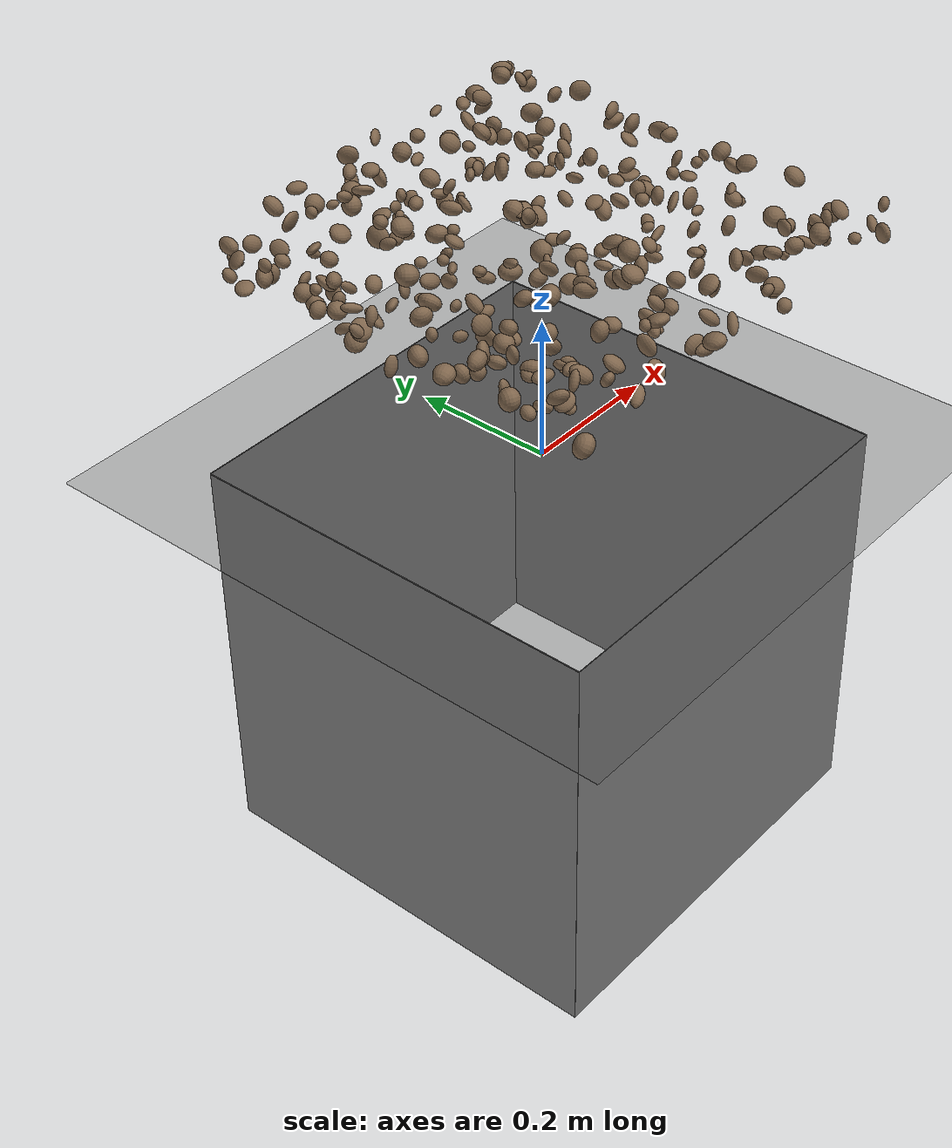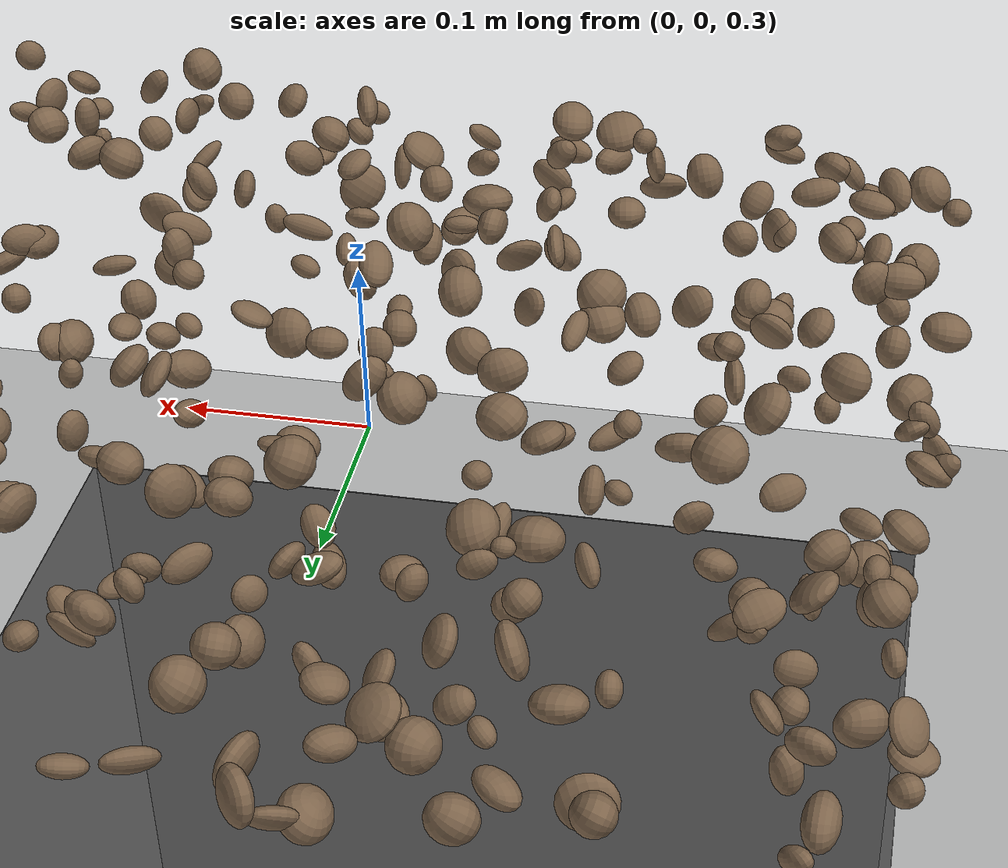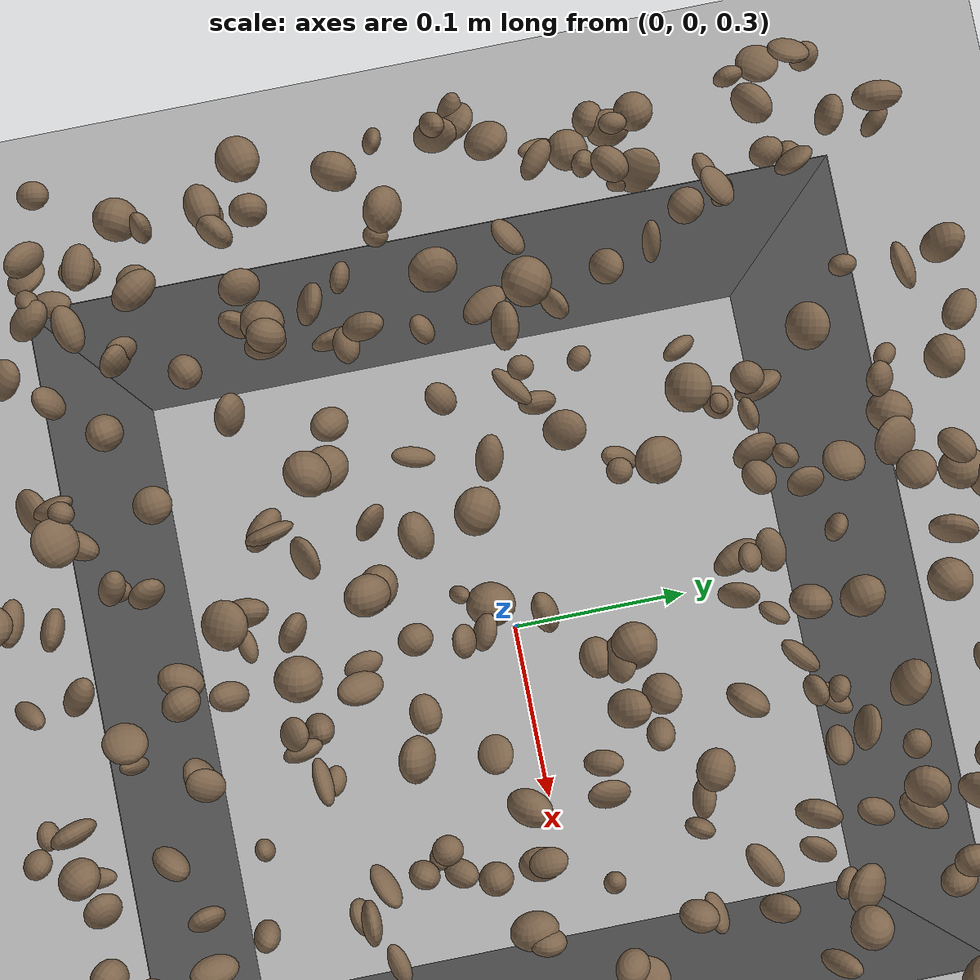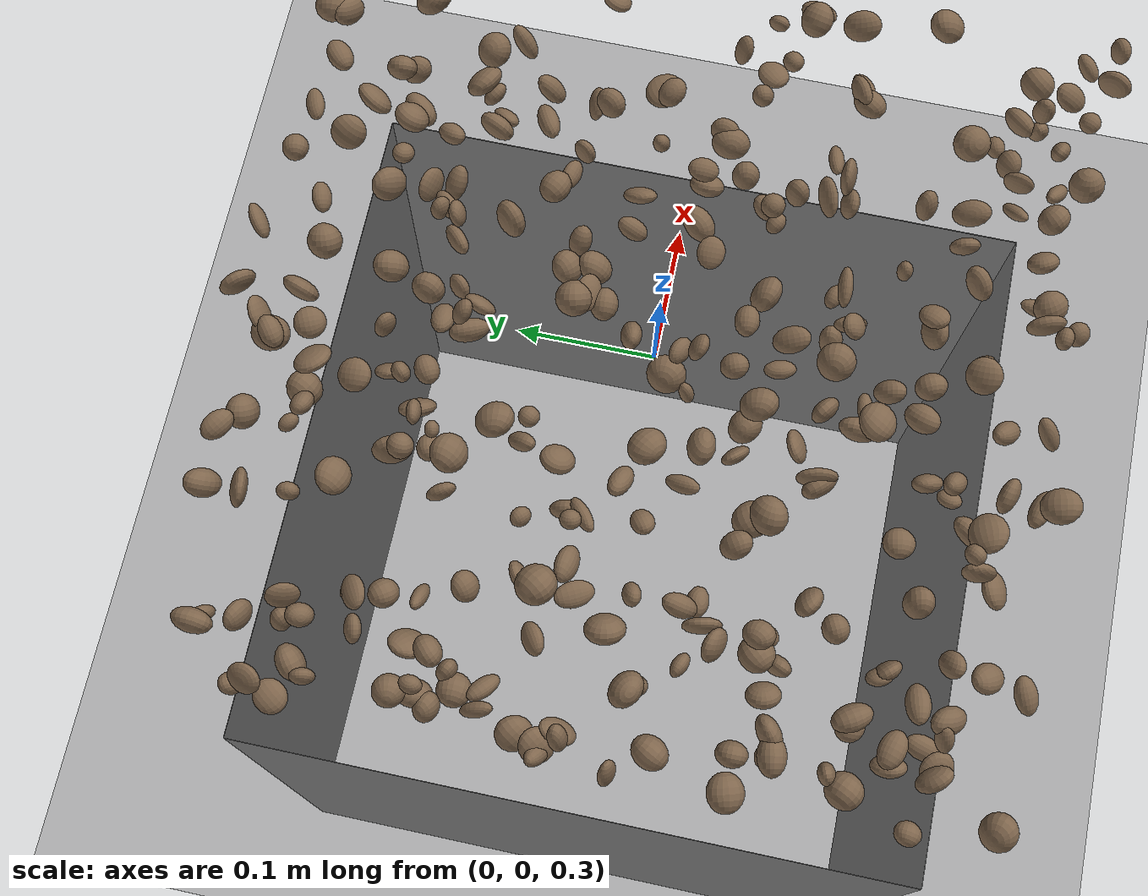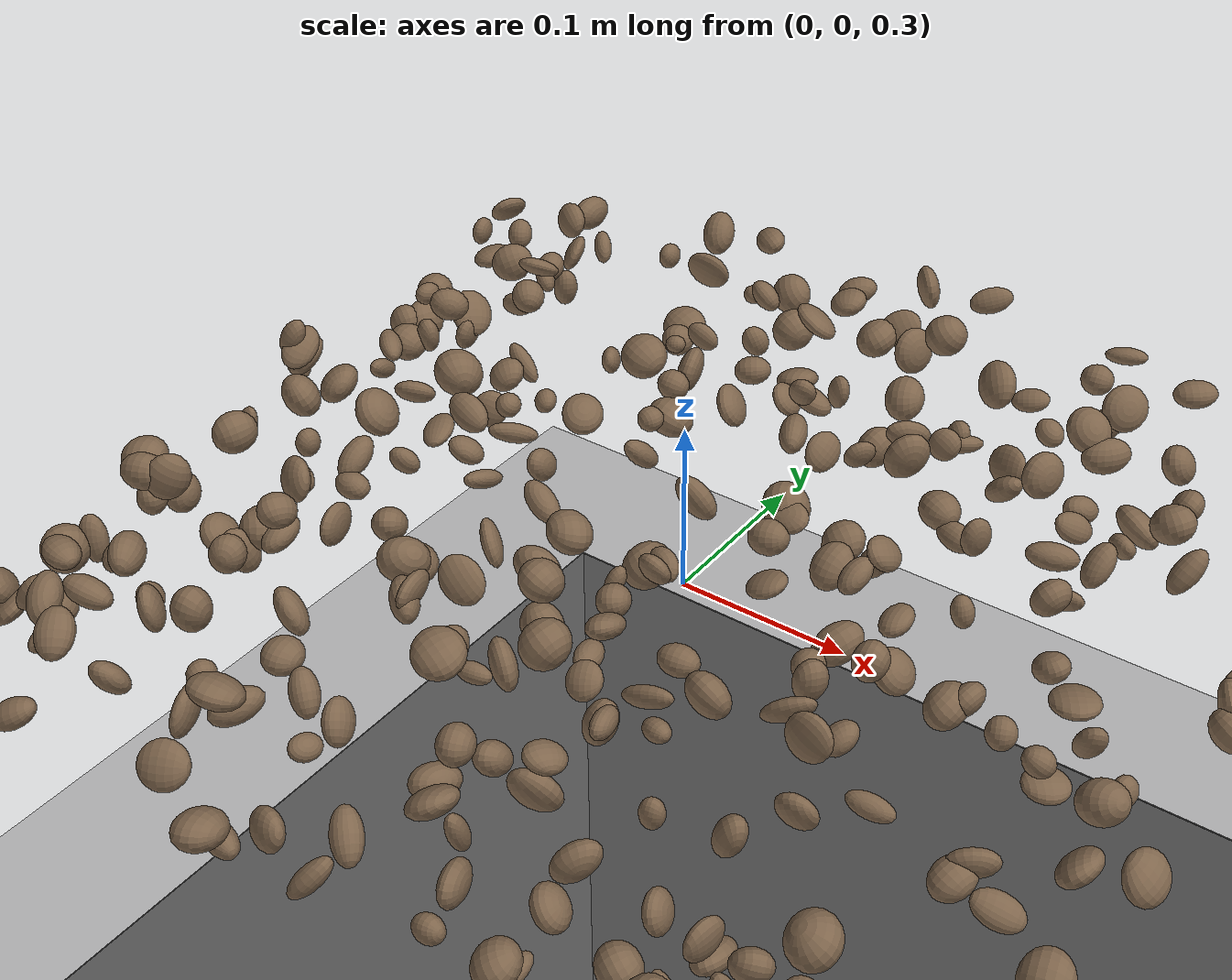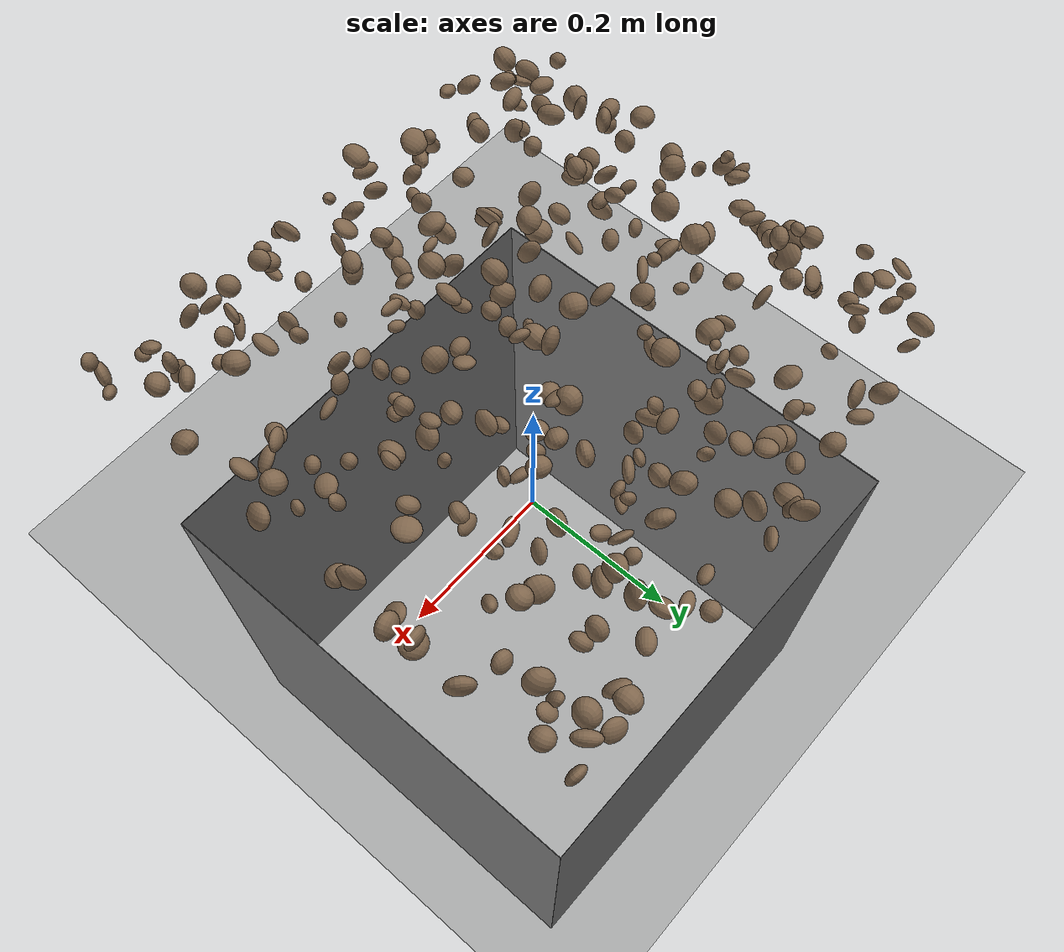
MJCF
<mujoco model="rocky_terrain_scene">
    <compiler angle="radian" inertiafromgeom="true" />
    <option timestep="0.002" gravity="0 0 -9.81" />

    <worldbody>
        <light name="sunlight" pos="5 5 5" dir="-1 -1 -1" diffuse="1 1 1" specular="0.5 0.5 0.5" ambient="0.5 0.5 0.5" />

        <geom name="ground_plane" type="plane" size="50 50 0.1" rgba="0.3 0.3 0.3 1" />

        <body name="rocky_terrain_body">

        </body>
    <body name="rock1" pos="-0.07783736164876834 0.09921915341333476 0.32363208690208123"><joint type="free" /><geom type="ellipsoid" size="0.011071342513922403 0.014658634273930344 0.013549575320532341" quat="0.06769836462464826 0.46464487154771883 0.13827851622941828 0.3293782475982147" rgba="0.5 0.4 0.3 1" /><inertial pos="-0.07783736164876834 0.09921915341333476 0.32363208690208123" quat="0.06769836462464826 0.46464487154771883 0.13827851622941828 0.3293782475982147" mass="5.1085522010993686e-05" /></body><body name="rock2" pos="-0.1618913933528302 0.2625176282600454 0.31849101172160393"><joint type="free" /><geom type="ellipsoid" size="0.00584001810640007 0.014340771354400893 0.01439611464920533" quat="0.13876416744154527 0.31011777069734786 0.2958686703900133 0.25524939147109355" rgba="0.5 0.4 0.3 1" /><inertial pos="-0.1618913933528302 0.2625176282600454 0.31849101172160393" quat="0.13876416744154527 0.31011777069734786 0.2958686703900133 0.25524939147109355" mass="4.4484271399576596e-05" /></body><body name="rock3" pos="-0.03223555336645467 -0.16077724797375317 0.34631018495878935"><joint type="free" /><geom type="ellipsoid" size="0.014626077566737016 0.009264446662391398 0.013909646098892892" quat="0.03998788990039249 0.1239420169796779 0.3374164144835095 0.4986536786364202" rgba="0.5 0.4 0.3 1" /><inertial pos="-0.03223555336645467 -0.16077724797375317 0.34631018495878935" quat="0.03998788990039249 0.1239420169796779 0.3374164144835095 0.4986536786364202" mass="6.521527341550346e-05" /></body><body name="rock4" pos="-0.13837743413212192 0.12309507766822592 0.32875486912103596"><joint type="free" /><geom type="ellipsoid" size="0.00537322995107435 0.008053958396853569 0.011455300996307032" quat="0.5064232320222981 0.2953588792906463 0.060601352686262724 0.13761653600079282" rgba="0.5 0.4 0.3 1" /><inertial pos="-0.13837743413212192 0.12309507766822592 0.32875486912103596" quat="0.5064232320222981 0.2953588792906463 0.060601352686262724 0.13761653600079282" mass="2.810040303795657e-05" /></body><body name="rock5" pos="-0.10491766481726925 0.1407069342135564 0.3142120019904226"><joint type="free" /><geom type="ellipsoid" size="0.008937921395637184 0.009156977080732967 0.00980627225927358" quat="0.20039090934611686 0.24079717355228192 0.31667632042528077 0.24213559667632054" rgba="0.5 0.4 0.3 1" /><inertial pos="-0.10491766481726925 0.1407069342135564 0.3142120019904226" quat="0.20039090934611686 0.24079717355228192 0.31667632042528077 0.24213559667632054" mass="5.9412650455157814e-05" /></body><body name="rock6" pos="-0.28456847063413515 0.009319998165489174 0.34258414885762006"><joint type="free" /><geom type="ellipsoid" size="0.005511186944710216 0.01442623861729482 0.010085508908504754" quat="0.2817506705743744 0.0804058118578011 0.47933603636555455 0.15850748120226998" rgba="0.5 0.4 0.3 1" /><inertial pos="-0.28456847063413515 0.009319998165489174 0.34258414885762006" quat="0.2817506705743744 0.0804058118578011 0.47933603636555455 0.15850748120226998" mass="9.179829487065379e-05" /></body><body name="rock7" pos="-0.19626988396241174 -0.19700658845404428 0.3208316382988301"><joint type="free" /><geom type="ellipsoid" size="0.006440900018989083 0.01360402493030283 0.011080643349734619" quat="0.3652797024681688 0.36046682763792925 0.09782211933153136 0.17643135056237064" rgba="0.5 0.4 0.3 1" /><inertial pos="-0.19626988396241174 -0.19700658845404428 0.3208316382988301" quat="0.3652797024681688 0.36046682763792925 0.09782211933153136 0.17643135056237064" mass="4.4402783090458106e-05" /></body><body name="rock8" pos="0.17515504475902904 -0.10252753923342997 0.31667931509111386"><joint type="free" /><geom type="ellipsoid" size="0.012820135661748291 0.006248273959211882 0.005544606150934452" quat="0.5900701840202651 0.29314471166963 0.0895342513500335 0.027250852960071383" rgba="0.5 0.4 0.3 1" /><inertial pos="0.17515504475902904 -0.10252753923342997 0.31667931509111386" quat="0.5900701840202651 0.29314471166963 0.0895342513500335 0.027250852960071383" mass="6.332326227197912e-05" /></body><body name="rock9" pos="0.0455991803744934 -0.13293479555035984 0.3222718424467396"><joint type="free" /><geom type="ellipsoid" size="0.01181557071446157 0.007402049026001079 0.005904650387028723" quat="0.249720134810362 0.19780634951662832 0.2839915829403999 0.26848193273260984" rgba="0.5 0.4 0.3 1" /><inertial pos="0.0455991803744934 -0.13293479555035984 0.3222718424467396" quat="0.249720134810362 0.19780634951662832 0.2839915829403999 0.26848193273260984" mass="6.739923988835503e-05" /></body><body name="rock10" pos="0.0931829318160412 -0.2174829539205336 0.3288720635041191"><joint type="free" /><geom type="ellipsoid" size="0.010039480525455755 0.013858479039491854 0.007651101145941109" quat="0.3513803623779936 0.2938398957158744 0.333134807815887 0.021644934090245007" rgba="0.5 0.4 0.3 1" /><inertial pos="0.0931829318160412 -0.2174829539205336 0.3288720635041191" quat="0.3513803623779936 0.2938398957158744 0.333134807815887 0.021644934090245007" mass="1.9637519690121844e-05" /></body><body name="rock11" pos="-0.2386879593044442 -0.17812819608723135 0.32411120275911925"><joint type="free" /><geom type="ellipsoid" size="0.01070129228785262 0.007661872606277605 0.01050466500610648" quat="0.24767641239833618 0.25410838125548746 0.16060269391667945 0.3376125124294969" rgba="0.5 0.4 0.3 1" /><inertial pos="-0.2386879593044442 -0.17812819608723135 0.32411120275911925" quat="0.24767641239833618 0.25410838125548746 0.16060269391667945 0.3376125124294969" mass="3.157293279690465e-05" /></body><body name="rock12" pos="0.28771409824334065 -0.2990879750585255 0.3068728130290085"><joint type="free" /><geom type="ellipsoid" size="0.01279246798379245 0.013513566375392465 0.006577625218572629" quat="0.22171978313817306 0.374262386509608 0.08779055782665456 0.3162272725255644" rgba="0.5 0.4 0.3 1" /><inertial pos="0.28771409824334065 -0.2990879750585255 0.3068728130290085" quat="0.22171978313817306 0.374262386509608 0.08779055782665456 0.3162272725255644" mass="8.489676141971232e-05" /></body><body name="rock13" pos="0.21563438266513485 0.29051332755488807 0.3322209444656196"><joint type="free" /><geom type="ellipsoid" size="0.010797178068012376 0.013842848045944815 0.012447171004049268" quat="0.05028895821512589 0.4118512236557666 0.06943988457126628 0.46841993355784134" rgba="0.5 0.4 0.3 1" /><inertial pos="0.21563438266513485 0.29051332755488807 0.3322209444656196" quat="0.05028895821512589 0.4118512236557666 0.06943988457126628 0.46841993355784134" mass="7.407023007421958e-05" /></body><body name="rock14" pos="-0.10565293591150393 0.27614101906744043 0.3130038783514849"><joint type="free" /><geom type="ellipsoid" size="0.011259315037727567 0.012988389328777987 0.012593919386957454" quat="0.40632951618774127 0.09151574337938839 0.2158103097101568 0.28634443072271354" rgba="0.5 0.4 0.3 1" /><inertial pos="-0.10565293591150393 0.27614101906744043 0.3130038783514849" quat="0.40632951618774127 0.09151574337938839 0.2158103097101568 0.28634443072271354" mass="5.690571913877134e-05" /></body><body name="rock15" pos="0.24148486530777274 -0.24560396250048633 0.32680259159923597"><joint type="free" /><geom type="ellipsoid" size="0.0080316698647097 0.007075033502217634 0.013645054902324358" quat="0.009070450597266416 0.5938436347394841 0.3908922956423392 0.006193619020910336" rgba="0.5 0.4 0.3 1" /><inertial pos="0.24148486530777274 -0.24560396250048633 0.32680259159923597" quat="0.009070450597266416 0.5938436347394841 0.3908922956423392 0.006193619020910336" mass="5.5573682787338826e-05" /></body><body name="rock16" pos="-0.2731474691029195 0.19573211708659877 0.31855908577705516"><joint type="free" /><geom type="ellipsoid" size="0.009818150184501988 0.012404059686263322 0.013625821147181374" quat="0.23342835564274786 0.10222056670209777 0.28348145322975965 0.3808696244253947" rgba="0.5 0.4 0.3 1" /><inertial pos="-0.2731474691029195 0.19573211708659877 0.31855908577705516" quat="0.23342835564274786 0.10222056670209777 0.28348145322975965 0.3808696244253947" mass="4.5166411818576996e-05" /></body><body name="rock17" pos="0.18560487403475878 0.11534283632474918 0.32333343446701124"><joint type="free" /><geom type="ellipsoid" size="0.00722948189314547 0.013614923601349114 0.008048506064945924" quat="0.3797691405620523 0.19423214719349752 0.3196407230341877 0.10635798921026249" rgba="0.5 0.4 0.3 1" /><inertial pos="0.18560487403475878 0.11534283632474918 0.32333343446701124" quat="0.3797691405620523 0.19423214719349752 0.3196407230341877 0.10635798921026249" mass="9.662338518383626e-05" /></body><body name="rock18" pos="0.06894355706067479 0.16014625375803615 0.3287854187330086"><joint type="free" /><geom type="ellipsoid" size="0.005842809830103462 0.009916705540305956 0.00920838911502294" quat="0.2079621102564696 0.2623365009301178 0.3808494204464724 0.14885196836694026" rgba="0.5 0.4 0.3 1" /><inertial pos="0.06894355706067479 0.16014625375803615 0.3287854187330086" quat="0.2079621102564696 0.2623365009301178 0.3808494204464724 0.14885196836694026" mass="1.4408811295064171e-05" /></body><body name="rock19" pos="0.026649117358798047 0.29461670237771115 0.34439276118656315"><joint type="free" /><geom type="ellipsoid" size="0.005409758007205418 0.007989228000487117 0.013554612765903438" quat="0.2713392611215606 0.08764500266321285 0.31390634417602603 0.3271093920392005" rgba="0.5 0.4 0.3 1" /><inertial pos="0.026649117358798047 0.29461670237771115 0.34439276118656315" quat="0.2713392611215606 0.08764500266321285 0.31390634417602603 0.3271093920392005" mass="5.460015563026169e-05" /></body><body name="rock20" pos="-0.011992708677216413 0.13640235144011348 0.3461877111608813"><joint type="free" /><geom type="ellipsoid" size="0.011034689027524962 0.006068225802496 0.007984416463388818" quat="0.3313923570840117 0.04604327415277894 0.48338737532017856 0.1391769934430307" rgba="0.5 0.4 0.3 1" /><inertial pos="-0.011992708677216413 0.13640235144011348 0.3461877111608813" quat="0.3313923570840117 0.04604327415277894 0.48338737532017856 0.1391769934430307" mass="9.254257290632136e-05" /></body><body name="rock21" pos="-0.24125547010139958 0.16142469300395806 0.31406485230197384"><joint type="free" /><geom type="ellipsoid" size="0.009154091653722933 0.005733449078898618 0.01056015097631682" quat="0.46366982334930285 0.03897787985464639 0.349422563996179 0.14792973279987182" rgba="0.5 0.4 0.3 1" /><inertial pos="-0.24125547010139958 0.16142469300395806 0.31406485230197384" quat="0.46366982334930285 0.03897787985464639 0.349422563996179 0.14792973279987182" mass="3.853466624625341e-05" /></body><body name="rock22" pos="0.13383248649731538 0.209013163575621 0.3369510705715921"><joint type="free" /><geom type="ellipsoid" size="0.013066379901754514 0.013937289431500039 0.009260013316514784" quat="0.4108624111185965 0.20393410260175543 0.0782244599984129 0.30697902628123513" rgba="0.5 0.4 0.3 1" /><inertial pos="0.13383248649731538 0.209013163575621 0.3369510705715921" quat="0.4108624111185965 0.20393410260175543 0.0782244599984129 0.30697902628123513" mass="2.8992146514211235e-05" /></body><body name="rock23" pos="0.15183992673948354 0.025943683118422545 0.3353860160259435"><joint type="free" /><geom type="ellipsoid" size="0.0062366066655846035 0.006200517002304943 0.0091474102471674" quat="0.08237339649162737 0.4110905249046813 0.4829224806957062 0.023613597907985125" rgba="0.5 0.4 0.3 1" /><inertial pos="0.15183992673948354 0.025943683118422545 0.3353860160259435" quat="0.08237339649162737 0.4110905249046813 0.4829224806957062 0.023613597907985125" mass="2.476426584903015e-05" /></body><body name="rock24" pos="0.17864908712597521 -0.017522451349978263 0.3220405006664266"><joint type="free" /><geom type="ellipsoid" size="0.010971112437279624 0.010305543358046971 0.0072740122215261376" quat="0.2049784018912644 0.3419760322435866 0.2692663806344574 0.18377918523069176" rgba="0.5 0.4 0.3 1" /><inertial pos="0.17864908712597521 -0.017522451349978263 0.3220405006664266" quat="0.2049784018912644 0.3419760322435866 0.2692663806344574 0.18377918523069176" mass="6.754304845414272e-05" /></body><body name="rock25" pos="0.17011046661070778 0.272056681943078 0.34180105928563187"><joint type="free" /><geom type="ellipsoid" size="0.009169754716967186 0.0075550017845514295 0.013065052781064547" quat="0.12730889305730547 0.18761528869022584 0.3261778101983539 0.3588980080541148" rgba="0.5 0.4 0.3 1" /><inertial pos="0.17011046661070778 0.272056681943078 0.34180105928563187" quat="0.12730889305730547 0.18761528869022584 0.3261778101983539 0.3588980080541148" mass="4.522741884029255e-05" /></body><body name="rock26" pos="0.006038750105745394 -0.19466955691593824 0.3334298120518721"><joint type="free" /><geom type="ellipsoid" size="0.011564689009995733 0.010396934480777397 0.00952352644815272" quat="0.2333427240896733 0.17273287438089333 0.3227203820268054 0.271204019502628" rgba="0.5 0.4 0.3 1" /><inertial pos="0.006038750105745394 -0.19466955691593824 0.3334298120518721" quat="0.2333427240896733 0.17273287438089333 0.3227203820268054 0.271204019502628" mass="9.82089657402298e-05" /></body><body name="rock27" pos="-0.09609055485822343 -0.24511559510547476 0.3499077601655817"><joint type="free" /><geom type="ellipsoid" size="0.01385994674220566 0.00783554175661948 0.0143015056460814" quat="0.24993972723229907 0.17087247450775836 0.3600618948142375 0.21912590344570507" rgba="0.5 0.4 0.3 1" /><inertial pos="-0.09609055485822343 -0.24511559510547476 0.3499077601655817" quat="0.24993972723229907 0.17087247450775836 0.3600618948142375 0.21912590344570507" mass="2.2570465909653566e-05" /></body><body name="rock28" pos="-0.10098911124908708 0.13703739088002553 0.34637706401248025"><joint type="free" /><geom type="ellipsoid" size="0.0051818435264927454 0.005332729601079422 0.006059376228078633" quat="0.22270788309223236 0.22431998683482968 0.226310429365351 0.32666170070758693" rgba="0.5 0.4 0.3 1" /><inertial pos="-0.10098911124908708 0.13703739088002553 0.34637706401248025" quat="0.22270788309223236 0.22431998683482968 0.226310429365351 0.32666170070758693" mass="6.995244773066065e-05" /></body><body name="rock29" pos="0.004371546944650306 -0.09025539088473272 0.31410864601411825"><joint type="free" /><geom type="ellipsoid" size="0.011732775088092378 0.007411257600204839 0.006027523236837113" quat="0.3603656682626726 0.07704888124016232 0.09399669743195325 0.46858875306521175" rgba="0.5 0.4 0.3 1" /><inertial pos="0.004371546944650306 -0.09025539088473272 0.31410864601411825" quat="0.3603656682626726 0.07704888124016232 0.09399669743195325 0.46858875306521175" mass="5.155025712867619e-05" /></body><body name="rock30" pos="-0.05040322202121894 0.1835128172988732 0.3016306647834519"><joint type="free" /><geom type="ellipsoid" size="0.012182648040962793 0.010758183568230866 0.005423660558059719" quat="0.44105506083024365 0.06301204517316805 0.2510845229608369 0.2448483710357513" rgba="0.5 0.4 0.3 1" /><inertial pos="-0.05040322202121894 0.1835128172988732 0.3016306647834519" quat="0.44105506083024365 0.06301204517316805 0.2510845229608369 0.2448483710357513" mass="3.1730355197173624e-05" /></body><body name="rock31" pos="0.29260020481804655 0.2995100324014594 0.3340357558037386"><joint type="free" /><geom type="ellipsoid" size="0.005861736936618548 0.01207101011058613 0.01121961871330374" quat="0.21172423093367626 0.3275830593818634 0.32767920160370084 0.1330135080807596" rgba="0.5 0.4 0.3 1" /><inertial pos="0.29260020481804655 0.2995100324014594 0.3340357558037386" quat="0.21172423093367626 0.3275830593818634 0.32767920160370084 0.1330135080807596" mass="6.174364384505471e-05" /></body><body name="rock32" pos="-0.20201556036843948 -0.10994990916520586 0.3170591177154268"><joint type="free" /><geom type="ellipsoid" size="0.012869876310503764 0.01195394485180225 0.013086724941724928" quat="0.08581249003234807 0.1975295950549179 0.34971730676780666 0.36694060814492735" rgba="0.5 0.4 0.3 1" /><inertial pos="-0.20201556036843948 -0.10994990916520586 0.3170591177154268" quat="0.08581249003234807 0.1975295950549179 0.34971730676780666 0.36694060814492735" mass="3.2189692201924075e-05" /></body><body name="rock33" pos="0.10218681069373614 0.032278116346205254 0.3457618540304527"><joint type="free" /><geom type="ellipsoid" size="0.013221572343394092 0.005744147040446012 0.00988953113502732" quat="0.2540882416299395 0.359873454888775 0.3597335352565308 0.026304768224754752" rgba="0.5 0.4 0.3 1" /><inertial pos="0.10218681069373614 0.032278116346205254 0.3457618540304527" quat="0.2540882416299395 0.359873454888775 0.3597335352565308 0.026304768224754752" mass="8.8759065911568e-05" /></body><body name="rock34" pos="-0.10457325265394785 -0.03836763652684344 0.34823730670663544"><joint type="free" /><geom type="ellipsoid" size="0.013026229787197946 0.005229465867460057 0.006331915909189897" quat="0.3970232489281601 0.12395192869362165 0.2161159216215976 0.2629089007566207" rgba="0.5 0.4 0.3 1" /><inertial pos="-0.10457325265394785 -0.03836763652684344 0.34823730670663544" quat="0.3970232489281601 0.12395192869362165 0.2161159216215976 0.2629089007566207" mass="5.976274800100497e-05" /></body><body name="rock35" pos="-0.1776243820405669 -0.06396175634785797 0.32853288437390904"><joint type="free" /><geom type="ellipsoid" size="0.010869782925749251 0.007783486549373196 0.007514523246065349" quat="0.8097167006723669 0.17890902220994304 0.005469345612311916 0.0059049315053781625" rgba="0.5 0.4 0.3 1" /><inertial pos="-0.1776243820405669 -0.06396175634785797 0.32853288437390904" quat="0.8097167006723669 0.17890902220994304 0.005469345612311916 0.0059049315053781625" mass="6.768445989533213e-05" /></body><body name="rock36" pos="-0.18479863299941585 -0.052465333133694336 0.33783387804255166"><joint type="free" /><geom type="ellipsoid" size="0.01383930681818036 0.007894468515133934 0.008165224818440795" quat="0.24267543917499707 0.2938707992052752 0.1068776625955787 0.3565760990241491" rgba="0.5 0.4 0.3 1" /><inertial pos="-0.18479863299941585 -0.052465333133694336 0.33783387804255166" quat="0.24267543917499707 0.2938707992052752 0.1068776625955787 0.3565760990241491" mass="1.1219393911225882e-05" /></body><body name="rock37" pos="-0.07020896939275564 -0.008652169929283415 0.3094387825622605"><joint type="free" /><geom type="ellipsoid" size="0.014692134584635544 0.01138990490542769 0.013181969834145393" quat="0.07777464812215536 0.15276247671550372 0.45230570084298494 0.3171571743193559" rgba="0.5 0.4 0.3 1" /><inertial pos="-0.07020896939275564 -0.008652169929283415 0.3094387825622605" quat="0.07777464812215536 0.15276247671550372 0.45230570084298494 0.3171571743193559" mass="8.36905491212762e-05" /></body><body name="rock38" pos="-0.2704464605187701 -0.12997347024977407 0.3378723338009091"><joint type="free" /><geom type="ellipsoid" size="0.010043951626641276 0.010714215796013862 0.014283837967510132" quat="0.27310123556058447 0.18411033521620193 0.27552475963750817 0.2672636695857055" rgba="0.5 0.4 0.3 1" /><inertial pos="-0.2704464605187701 -0.12997347024977407 0.3378723338009091" quat="0.27310123556058447 0.18411033521620193 0.27552475963750817 0.2672636695857055" mass="1.7372968839587142e-05" /></body><body name="rock39" pos="-0.020278214450456633 0.19359313382978227 0.31286325412313204"><joint type="free" /><geom type="ellipsoid" size="0.0057785309721640745 0.011387626264453016 0.008507181034245493" quat="0.2962415256555715 0.38634390938606555 0.20632973238327312 0.1110848325750899" rgba="0.5 0.4 0.3 1" /><inertial pos="-0.020278214450456633 0.19359313382978227 0.31286325412313204" quat="0.2962415256555715 0.38634390938606555 0.20632973238327312 0.1110848325750899" mass="8.440477672930341e-05" /></body><body name="rock40" pos="-0.22313421847379084 0.16144716325241604 0.3472089300675655"><joint type="free" /><geom type="ellipsoid" size="0.00977876973510864 0.0050780563228770715 0.012838535522750178" quat="0.2566743835053161 0.08337261419473652 0.43043016510982385 0.22952283719012356" rgba="0.5 0.4 0.3 1" /><inertial pos="-0.22313421847379084 0.16144716325241604 0.3472089300675655" quat="0.2566743835053161 0.08337261419473652 0.43043016510982385 0.22952283719012356" mass="9.752249279148137e-05" /></body><body name="rock41" pos="0.17147197121123686 -0.023458773102510877 0.31882288414462806"><joint type="free" /><geom type="ellipsoid" size="0.014264060609615013 0.011869493720880423 0.010775289101009982" quat="0.15292445887733805 0.32807882048982884 0.3367537088918468 0.18224301174098634" rgba="0.5 0.4 0.3 1" /><inertial pos="0.17147197121123686 -0.023458773102510877 0.31882288414462806" quat="0.15292445887733805 0.32807882048982884 0.3367537088918468 0.18224301174098634" mass="4.2088040123815106e-05" /></body><body name="rock42" pos="-0.14404916084010655 0.06577340944788534 0.32771470176231265"><joint type="free" /><geom type="ellipsoid" size="0.005949833813480584 0.007056469004255389 0.007732787381990881" quat="0.3817039309784606 0.30718782986987897 0.2839269431238226 0.027181296027837788" rgba="0.5 0.4 0.3 1" /><inertial pos="-0.14404916084010655 0.06577340944788534 0.32771470176231265" quat="0.3817039309784606 0.30718782986987897 0.2839269431238226 0.027181296027837788" mass="4.196520457768441e-05" /></body><body name="rock43" pos="-0.08138473165811455 -0.13013188346628152 0.33638000553877523"><joint type="free" /><geom type="ellipsoid" size="0.007840714041864085 0.010550151283558129 0.014274807938575048" quat="0.3200400703448491 0.384043427524407 0.1398153508549261 0.15610115127581778" rgba="0.5 0.4 0.3 1" /><inertial pos="-0.08138473165811455 -0.13013188346628152 0.33638000553877523" quat="0.3200400703448491 0.384043427524407 0.1398153508549261 0.15610115127581778" mass="1.7791521030825956e-05" /></body><body name="rock44" pos="0.00254802885095029 -0.03055004246422577 0.33059809048420236"><joint type="free" /><geom type="ellipsoid" size="0.010793925513202265 0.005777974245367568 0.00978156889054224" quat="0.3777492152204831 0.10938182317907874 0.44023170773352627 0.07263725386691178" rgba="0.5 0.4 0.3 1" /><inertial pos="0.00254802885095029 -0.03055004246422577 0.33059809048420236" quat="0.3777492152204831 0.10938182317907874 0.44023170773352627 0.07263725386691178" mass="6.103472233864933e-05" /></body><body name="rock45" pos="-0.06075936909536117 -0.1093565382766842 0.3449818065129015"><joint type="free" /><geom type="ellipsoid" size="0.005331376584958294 0.014064668016761463 0.011705495791244297" quat="0.3192149862019449 0.03396373257032251 0.2608173169554617 0.3860039642722709" rgba="0.5 0.4 0.3 1" /><inertial pos="-0.06075936909536117 -0.1093565382766842 0.3449818065129015" quat="0.3192149862019449 0.03396373257032251 0.2608173169554617 0.3860039642722709" mass="6.830739937448714e-05" /></body><body name="rock46" pos="0.2883189223521729 0.04199688131916324 0.3317737885481291"><joint type="free" /><geom type="ellipsoid" size="0.006914031462563348 0.014460144672101636 0.013487459560239431" quat="0.18985410807480813 0.567226370463646 0.1026632800775782 0.1402562413839677" rgba="0.5 0.4 0.3 1" /><inertial pos="0.2883189223521729 0.04199688131916324 0.3317737885481291" quat="0.18985410807480813 0.567226370463646 0.1026632800775782 0.1402562413839677" mass="9.134906311458507e-05" /></body><body name="rock47" pos="0.29431228590379505 -0.2923366566538984 0.3412502313523401"><joint type="free" /><geom type="ellipsoid" size="0.009045318687157886 0.009814737697087425 0.006488334093415866" quat="0.38911242382664024 0.40436840590253853 0.18891402303382113 0.01760514723700014" rgba="0.5 0.4 0.3 1" /><inertial pos="0.29431228590379505 -0.2923366566538984 0.3412502313523401" quat="0.38911242382664024 0.40436840590253853 0.18891402303382113 0.01760514723700014" mass="9.262350387092702e-05" /></body><body name="rock48" pos="-0.005961197681106811 0.2598470982005933 0.3138445969464796"><joint type="free" /><geom type="ellipsoid" size="0.014364666551371433 0.01487325003603612 0.007111191061896421" quat="0.2693752621792722 0.29895368748580514 0.12330066901563054 0.3083703813192921" rgba="0.5 0.4 0.3 1" /><inertial pos="-0.005961197681106811 0.2598470982005933 0.3138445969464796" quat="0.2693752621792722 0.29895368748580514 0.12330066901563054 0.3083703813192921" mass="4.98397376255456e-05" /></body><body name="rock49" pos="-0.04035492479244912 0.2751807453341148 0.30310520255382467"><joint type="free" /><geom type="ellipsoid" size="0.014438839342624573 0.013182663164758145 0.011290137725669426" quat="0.11849150815230383 0.35519807231102746 0.3974956807346511 0.12881473880201771" rgba="0.5 0.4 0.3 1" /><inertial pos="-0.04035492479244912 0.2751807453341148 0.30310520255382467" quat="0.11849150815230383 0.35519807231102746 0.3974956807346511 0.12881473880201771" mass="6.209405805702146e-05" /></body><body name="rock50" pos="0.08036896505584601 -0.29709001053637163 0.3032808204155918"><joint type="free" /><geom type="ellipsoid" size="0.00889568039373 0.009555926474670417 0.007414247570193107" quat="0.08596008894657244 0.2781041538774733 0.4006575246556521 0.2352782325203021" rgba="0.5 0.4 0.3 1" /><inertial pos="0.08036896505584601 -0.29709001053637163 0.3032808204155918" quat="0.08596008894657244 0.2781041538774733 0.4006575246556521 0.2352782325203021" mass="2.8589221094264946e-05" /></body><body name="rock51" pos="-0.007251525823545268 -0.19638937622609837 0.30410935727310434"><joint type="free" /><geom type="ellipsoid" size="0.013781156964046665 0.009582293146231876 0.010262443326852213" quat="0.41511117420185534 0.17651105520621366 0.17520895808475614 0.2331688125071748" rgba="0.5 0.4 0.3 1" /><inertial pos="-0.007251525823545268 -0.19638937622609837 0.30410935727310434" quat="0.41511117420185534 0.17651105520621366 0.17520895808475614 0.2331688125071748" mass="8.880050158606355e-05" /></body><body name="rock52" pos="-0.09397048577227385 -0.23623991821211576 0.33537955853088547"><joint type="free" /><geom type="ellipsoid" size="0.014627517150022671 0.0088052420966401 0.007998407114503812" quat="0.29525056692931595 0.34646047513327566 0.13713399722753722 0.22115496070987117" rgba="0.5 0.4 0.3 1" /><inertial pos="-0.09397048577227385 -0.23623991821211576 0.33537955853088547" quat="0.29525056692931595 0.34646047513327566 0.13713399722753722 0.22115496070987117" mass="4.313412998773216e-05" /></body><body name="rock53" pos="-0.25277261687575636 0.23401982033320473 0.33947924739612073"><joint type="free" /><geom type="ellipsoid" size="0.006944259811388688 0.010968925238899054 0.011911474111878203" quat="0.27321578250142015 0.33093504752046315 0.2932088140257815 0.10264035595233524" rgba="0.5 0.4 0.3 1" /><inertial pos="-0.25277261687575636 0.23401982033320473 0.33947924739612073" quat="0.27321578250142015 0.33093504752046315 0.2932088140257815 0.10264035595233524" mass="5.786083434143449e-05" /></body><body name="rock54" pos="0.24825165446746084 -0.2837306608059507 0.3114851914091278"><joint type="free" /><geom type="ellipsoid" size="0.00818244212188936 0.006880144571705261 0.00785306060353977" quat="0.31165126986639274 0.2781555107745317 0.15713971436353222 0.2530535049955433" rgba="0.5 0.4 0.3 1" /><inertial pos="0.24825165446746084 -0.2837306608059507 0.3114851914091278" quat="0.31165126986639274 0.2781555107745317 0.15713971436353222 0.2530535049955433" mass="4.393823296322525e-05" /></body><body name="rock55" pos="-0.15215750213808604 -0.2068169126895992 0.34751264931397047"><joint type="free" /><geom type="ellipsoid" size="0.010382706784410667 0.013520486599849366 0.010503050185054144" quat="0.18169178802625427 0.27889622620261956 0.275017781794774 0.2643942039763522" rgba="0.5 0.4 0.3 1" /><inertial pos="-0.15215750213808604 -0.2068169126895992 0.34751264931397047" quat="0.18169178802625427 0.27889622620261956 0.275017781794774 0.2643942039763522" mass="4.013417718846578e-05" /></body><body name="rock56" pos="0.1642038926566377 -0.23878968136460527 0.309684594825866"><joint type="free" /><geom type="ellipsoid" size="0.005773173364998719 0.005135282509921176 0.013516365435329483" quat="0.028891275726018406 0.3282719085754038 0.38738861869466057 0.25544819700391724" rgba="0.5 0.4 0.3 1" /><inertial pos="0.1642038926566377 -0.23878968136460527 0.309684594825866" quat="0.028891275726018406 0.3282719085754038 0.38738861869466057 0.25544819700391724" mass="4.431072304298237e-05" /></body><body name="rock57" pos="-0.029760248552522572 0.2850999275501383 0.30936433106114936"><joint type="free" /><geom type="ellipsoid" size="0.005114251742777985 0.010990446564528904 0.014058180401262613" quat="0.35381487693604674 0.04104748576433659 0.2724656114106549 0.3326720258889617" rgba="0.5 0.4 0.3 1" /><inertial pos="-0.029760248552522572 0.2850999275501383 0.30936433106114936" quat="0.35381487693604674 0.04104748576433659 0.2724656114106549 0.3326720258889617" mass="7.411917166257122e-05" /></body><body name="rock58" pos="-0.23217087734913608 0.20999055826269314 0.33249065745509654"><joint type="free" /><geom type="ellipsoid" size="0.012258994537243027 0.00507976864965245 0.010915279452059647" quat="0.3073963002286425 0.1688508745349913 0.05748455398940219 0.46626827124696407" rgba="0.5 0.4 0.3 1" /><inertial pos="-0.23217087734913608 0.20999055826269314 0.33249065745509654" quat="0.3073963002286425 0.1688508745349913 0.05748455398940219 0.46626827124696407" mass="3.989500182363149e-05" /></body><body name="rock59" pos="-0.2012357008470429 -0.19253952140966887 0.32266238074066167"><joint type="free" /><geom type="ellipsoid" size="0.009634667353418882 0.005536058165906742 0.008413988602330558" quat="0.1379066506341024 0.2995510397192142 0.44498709855258767 0.1175552110940957" rgba="0.5 0.4 0.3 1" /><inertial pos="-0.2012357008470429 -0.19253952140966887 0.32266238074066167" quat="0.1379066506341024 0.2995510397192142 0.44498709855258767 0.1175552110940957" mass="7.079817709330657e-05" /></body><body name="rock60" pos="-0.23883139633864078 -0.23050638754328676 0.30540697295977315"><joint type="free" /><geom type="ellipsoid" size="0.012986393095322537 0.006445842518577323 0.008598355493890021" quat="0.31721086887196354 0.25370510765533943 0.11765319197903329 0.31143083149366374" rgba="0.5 0.4 0.3 1" /><inertial pos="-0.23883139633864078 -0.23050638754328676 0.30540697295977315" quat="0.31721086887196354 0.25370510765533943 0.11765319197903329 0.31143083149366374" mass="8.520241319868806e-05" /></body><body name="rock61" pos="0.11602653572098337 0.0851900250544731 0.3303472378638166"><joint type="free" /><geom type="ellipsoid" size="0.005658893891841106 0.0075318138313646196 0.011867280667505383" quat="0.3436979760385124 0.2067485846801409 0.33748111260433583 0.11207232667701081" rgba="0.5 0.4 0.3 1" /><inertial pos="0.11602653572098337 0.0851900250544731 0.3303472378638166" quat="0.3436979760385124 0.2067485846801409 0.33748111260433583 0.11207232667701081" mass="6.84170566113914e-05" /></body><body name="rock62" pos="-0.05986189859301727 -0.2044178369401884 0.32001551729606004"><joint type="free" /><geom type="ellipsoid" size="0.006880434857586668 0.010329481340200581 0.012495955848579784" quat="0.21341283756428142 0.6197470754800234 0.03623488822941311 0.13060519872628207" rgba="0.5 0.4 0.3 1" /><inertial pos="-0.05986189859301727 -0.2044178369401884 0.32001551729606004" quat="0.21341283756428142 0.6197470754800234 0.03623488822941311 0.13060519872628207" mass="1.2205629685018155e-05" /></body><body name="rock63" pos="0.06446563226998209 -0.12341398315326649 0.3414018675829372"><joint type="free" /><geom type="ellipsoid" size="0.005190683584739645 0.0067826076162895085 0.014533168561687248" quat="0.23474647396942128 0.22791196019473067 0.19291657573038892 0.34442499010545913" rgba="0.5 0.4 0.3 1" /><inertial pos="0.06446563226998209 -0.12341398315326649 0.3414018675829372" quat="0.23474647396942128 0.22791196019473067 0.19291657573038892 0.34442499010545913" mass="9.884855393567706e-05" /></body><body name="rock64" pos="-0.11071343541079562 -0.09014950314796547 0.32069993406835906"><joint type="free" /><geom type="ellipsoid" size="0.014633736854413115 0.011064164697440777 0.012881467324175597" quat="0.21556301274062167 0.15117840604062954 0.34927897324739576 0.28397960797135297" rgba="0.5 0.4 0.3 1" /><inertial pos="-0.11071343541079562 -0.09014950314796547 0.32069993406835906" quat="0.21556301274062167 0.15117840604062954 0.34927897324739576 0.28397960797135297" mass="6.268022669564751e-05" /></body><body name="rock65" pos="0.06393887346470256 -0.07083406186291813 0.3045079179791113"><joint type="free" /><geom type="ellipsoid" size="0.009806300191709815 0.014317924199624184 0.013922801473246975" quat="0.18916573857097047 0.3674562427285102 0.20026315983669457 0.2431148588638248" rgba="0.5 0.4 0.3 1" /><inertial pos="0.06393887346470256 -0.07083406186291813 0.3045079179791113" quat="0.18916573857097047 0.3674562427285102 0.20026315983669457 0.2431148588638248" mass="2.075234942752638e-05" /></body><body name="rock66" pos="-0.22463461262950546 -0.2384466676029476 0.3416070646038598"><joint type="free" /><geom type="ellipsoid" size="0.008638670220083905 0.01449554756722957 0.010006570857014145" quat="0.47486349156851865 0.07548660877039705 0.2519205869165209 0.19772931274456337" rgba="0.5 0.4 0.3 1" /><inertial pos="-0.22463461262950546 -0.2384466676029476 0.3416070646038598" quat="0.47486349156851865 0.07548660877039705 0.2519205869165209 0.19772931274456337" mass="1.1103388222379317e-05" /></body><body name="rock67" pos="0.10304445684257363 -0.012337731490724146 0.316767117461709"><joint type="free" /><geom type="ellipsoid" size="0.010454585343681405 0.01475948535027307 0.010365506594237354" quat="0.26181873092832475 0.220013718013094 0.4629151868290933 0.05525236422948791" rgba="0.5 0.4 0.3 1" /><inertial pos="0.10304445684257363 -0.012337731490724146 0.316767117461709" quat="0.26181873092832475 0.220013718013094 0.4629151868290933 0.05525236422948791" mass="5.0220566640785715e-05" /></body><body name="rock68" pos="-0.1118606478036416 -0.23906016418635556 0.3482980172118586"><joint type="free" /><geom type="ellipsoid" size="0.007491681224793158 0.007709993122884104 0.006830563989145374" quat="0.3555708089896789 0.2653178456915564 0.2844671281753497 0.09464421714341503" rgba="0.5 0.4 0.3 1" /><inertial pos="-0.1118606478036416 -0.23906016418635556 0.3482980172118586" quat="0.3555708089896789 0.2653178456915564 0.2844671281753497 0.09464421714341503" mass="4.1944708104586967e-05" /></body><body name="rock69" pos="0.29973003306866913 0.18109862482074085 0.33874339170117107"><joint type="free" /><geom type="ellipsoid" size="0.0078792401902755 0.014392967742478426 0.014303873561181547" quat="0.3631425634841725 0.32828418797916975 0.1532296778439232 0.15534357069273452" rgba="0.5 0.4 0.3 1" /><inertial pos="0.29973003306866913 0.18109862482074085 0.33874339170117107" quat="0.3631425634841725 0.32828418797916975 0.1532296778439232 0.15534357069273452" mass="8.064206073787483e-05" /></body><body name="rock70" pos="0.2515899899955109 0.2757683592658731 0.34933988375306313"><joint type="free" /><geom type="ellipsoid" size="0.01262946569943713 0.014384770925173703 0.011262634036022637" quat="0.1537330845439228 0.19571600983636409 0.16694675927244185 0.4836041463472712" rgba="0.5 0.4 0.3 1" /><inertial pos="0.2515899899955109 0.2757683592658731 0.34933988375306313" quat="0.1537330845439228 0.19571600983636409 0.16694675927244185 0.4836041463472712" mass="2.297552910089349e-05" /></body><body name="rock71" pos="-0.19166962583709007 -0.10827611447428023 0.3317877492019867"><joint type="free" /><geom type="ellipsoid" size="0.011663055445287757 0.00988634691531409 0.01018223915076541" quat="0.25465794269361797 0.33900886108969236 0.33251850279165285 0.07381469342503678" rgba="0.5 0.4 0.3 1" /><inertial pos="-0.19166962583709007 -0.10827611447428023 0.3317877492019867" quat="0.25465794269361797 0.33900886108969236 0.33251850279165285 0.07381469342503678" mass="4.907499433474973e-05" /></body><body name="rock72" pos="0.06558993905257854 -0.26621712733886665 0.34022840399700377"><joint type="free" /><geom type="ellipsoid" size="0.014030265594740066 0.010585309305466745 0.006252331926162075" quat="0.25336560987824647 0.1666961508584066 0.31872563331839693 0.26121260594495" rgba="0.5 0.4 0.3 1" /><inertial pos="0.06558993905257854 -0.26621712733886665 0.34022840399700377" quat="0.25336560987824647 0.1666961508584066 0.31872563331839693 0.26121260594495" mass="4.550847871957711e-05" /></body><body name="rock73" pos="-0.042363410062458084 0.2386250169268917 0.3465184545536174"><joint type="free" /><geom type="ellipsoid" size="0.011270663612466189 0.007130606179602782 0.011572516218522313" quat="0.38557886870613856 0.43011945130181817 0.02676875598728677 0.15753292400475652" rgba="0.5 0.4 0.3 1" /><inertial pos="-0.042363410062458084 0.2386250169268917 0.3465184545536174" quat="0.38557886870613856 0.43011945130181817 0.02676875598728677 0.15753292400475652" mass="3.545918605399998e-05" /></body><body name="rock74" pos="-0.2560841925257443 -0.12557390756526238 0.3377121006480003"><joint type="free" /><geom type="ellipsoid" size="0.007820467037922173 0.012469223615264868 0.01458216509128566" quat="0.2687887561688254 0.05256434201535092 0.14690794034665602 0.5317389614691675" rgba="0.5 0.4 0.3 1" /><inertial pos="-0.2560841925257443 -0.12557390756526238 0.3377121006480003" quat="0.2687887561688254 0.05256434201535092 0.14690794034665602 0.5317389614691675" mass="3.5814317895969625e-05" /></body><body name="rock75" pos="0.07713836982099642 0.0704167044031202 0.3050539852802112"><joint type="free" /><geom type="ellipsoid" size="0.00830376147026858 0.007883298388161805 0.012511967429454037" quat="0.40174769006679 0.14191402353554586 0.0932999440292852 0.363038342368379" rgba="0.5 0.4 0.3 1" /><inertial pos="0.07713836982099642 0.0704167044031202 0.3050539852802112" quat="0.40174769006679 0.14191402353554586 0.0932999440292852 0.363038342368379" mass="4.290153047709332e-05" /></body><body name="rock76" pos="0.03508166958622205 -0.22896852389727484 0.32190977714277397"><joint type="free" /><geom type="ellipsoid" size="0.006045314872125101 0.013998728674394709 0.005054581880906834" quat="0.18458535492278674 0.2562540842333875 0.23152675959185484 0.3276338012519708" rgba="0.5 0.4 0.3 1" /><inertial pos="0.03508166958622205 -0.22896852389727484 0.32190977714277397" quat="0.18458535492278674 0.2562540842333875 0.23152675959185484 0.3276338012519708" mass="7.739475256607368e-05" /></body><body name="rock77" pos="0.09677161015326219 -0.16523567388198196 0.3178232740086251"><joint type="free" /><geom type="ellipsoid" size="0.005628872786170601 0.009325726308973633 0.006599649616555323" quat="0.2069103195840084 0.23521027600029734 0.2861780218572462 0.271701382558448" rgba="0.5 0.4 0.3 1" /><inertial pos="0.09677161015326219 -0.16523567388198196 0.3178232740086251" quat="0.2069103195840084 0.23521027600029734 0.2861780218572462 0.271701382558448" mass="3.584243700939838e-05" /></body><body name="rock78" pos="-0.004599881245214488 -0.2835164661440777 0.3152932514876237"><joint type="free" /><geom type="ellipsoid" size="0.01437930644892688 0.006586437114828266 0.005928474954694481" quat="0.036704996859754875 0.5385235591859472 0.16212131445646788 0.26265012949783" rgba="0.5 0.4 0.3 1" /><inertial pos="-0.004599881245214488 -0.2835164661440777 0.3152932514876237" quat="0.036704996859754875 0.5385235591859472 0.16212131445646788 0.26265012949783" mass="9.754463296947357e-05" /></body><body name="rock79" pos="-0.16792720440164993 0.28349179451137146 0.33487691019115917"><joint type="free" /><geom type="ellipsoid" size="0.010102598031248196 0.014478762038006871 0.01026636698889375" quat="0.41967800101947267 0.13604088973700626 0.26431491670669854 0.17996619253682258" rgba="0.5 0.4 0.3 1" /><inertial pos="-0.16792720440164993 0.28349179451137146 0.33487691019115917" quat="0.41967800101947267 0.13604088973700626 0.26431491670669854 0.17996619253682258" mass="2.255868112413753e-05" /></body><body name="rock80" pos="0.03908087118714154 -0.06080448147503656 0.30771802652144353"><joint type="free" /><geom type="ellipsoid" size="0.009232555201978562 0.008676918383044664 0.011825441986944466" quat="0.2802510693054295 0.1989021409285679 0.2898090904776834 0.23103769928831933" rgba="0.5 0.4 0.3 1" /><inertial pos="0.03908087118714154 -0.06080448147503656 0.30771802652144353" quat="0.2802510693054295 0.1989021409285679 0.2898090904776834 0.23103769928831933" mass="4.690565523389559e-05" /></body><body name="rock81" pos="0.29361205378070937 0.11999695158641382 0.3173956772952905"><joint type="free" /><geom type="ellipsoid" size="0.01484225084494362 0.008907189258945571 0.014249741341085604" quat="0.2500427786363554 0.09897500720996351 0.4316335388453645 0.2193486753083166" rgba="0.5 0.4 0.3 1" /><inertial pos="0.29361205378070937 0.11999695158641382 0.3173956772952905" quat="0.2500427786363554 0.09897500720996351 0.4316335388453645 0.2193486753083166" mass="2.8571196499621467e-05" /></body><body name="rock82" pos="-0.17890561808467587 -0.15682720197785147 0.33865111509254064"><joint type="free" /><geom type="ellipsoid" size="0.010006634042224665 0.010931197280108287 0.009378831455147663" quat="0.4608411797713853 0.37024921118066134 0.14919501146068068 0.019714597587272703" rgba="0.5 0.4 0.3 1" /><inertial pos="-0.17890561808467587 -0.15682720197785147 0.33865111509254064" quat="0.4608411797713853 0.37024921118066134 0.14919501146068068 0.019714597587272703" mass="7.500084360591762e-05" /></body><body name="rock83" pos="-0.25157524036917245 0.26698626001798625 0.30487395394411765"><joint type="free" /><geom type="ellipsoid" size="0.005665995093383538 0.011344883570904428 0.0067349438910503665" quat="0.4936331626841036 0.1662624349025706 0.1237042468933144 0.2164001555200114" rgba="0.5 0.4 0.3 1" /><inertial pos="-0.25157524036917245 0.26698626001798625 0.30487395394411765" quat="0.4936331626841036 0.1662624349025706 0.1237042468933144 0.2164001555200114" mass="4.3988870089183516e-05" /></body><body name="rock84" pos="0.20554206772391131 0.16346095761980822 0.3294756805848347"><joint type="free" /><geom type="ellipsoid" size="0.012308185908009212 0.013296476543496392 0.010986886266939909" quat="0.1616333624033626 0.45179856019452813 0.29074535740570967 0.09582271999639967" rgba="0.5 0.4 0.3 1" /><inertial pos="0.20554206772391131 0.16346095761980822 0.3294756805848347" quat="0.1616333624033626 0.45179856019452813 0.29074535740570967 0.09582271999639967" mass="5.991559400491326e-05" /></body><body name="rock85" pos="-0.06501522359419581 -0.21894493782762253 0.3462788939371595"><joint type="free" /><geom type="ellipsoid" size="0.007440229564905042 0.00799400382590525 0.01258519051699666" quat="0.19322853650999366 0.4237796855633382 0.33078263511800493 0.0522091428086632" rgba="0.5 0.4 0.3 1" /><inertial pos="-0.06501522359419581 -0.21894493782762253 0.3462788939371595" quat="0.19322853650999366 0.4237796855633382 0.33078263511800493 0.0522091428086632" mass="5.415982826313212e-05" /></body><body name="rock86" pos="0.22367218886714918 0.1441203896607861 0.31798929756509364"><joint type="free" /><geom type="ellipsoid" size="0.006987325096251715 0.007597090894354005 0.01476574228355004" quat="0.22495770777546778 0.035700128408838204 0.21079066310061723 0.5285515007150767" rgba="0.5 0.4 0.3 1" /><inertial pos="0.22367218886714918 0.1441203896607861 0.31798929756509364" quat="0.22495770777546778 0.035700128408838204 0.21079066310061723 0.5285515007150767" mass="5.654457668755571e-05" /></body><body name="rock87" pos="0.07417681224037509 0.21066235094804714 0.3446939570924775"><joint type="free" /><geom type="ellipsoid" size="0.00887115620419494 0.012627015536750719 0.014277643640964455" quat="0.26014989067328126 0.4170600788871697 0.309548793672182 0.013241236767366923" rgba="0.5 0.4 0.3 1" /><inertial pos="0.07417681224037509 0.21066235094804714 0.3446939570924775" quat="0.26014989067328126 0.4170600788871697 0.309548793672182 0.013241236767366923" mass="6.225515986725297e-05" /></body><body name="rock88" pos="0.1469640516921391 0.2063802510995642 0.32631144392907036"><joint type="free" /><geom type="ellipsoid" size="0.014899337928428933 0.009028351673751777 0.010423919822584556" quat="0.0763749713113944 0.6078504632323938 0.2790282633623279 0.03674630209388395" rgba="0.5 0.4 0.3 1" /><inertial pos="0.1469640516921391 0.2063802510995642 0.32631144392907036" quat="0.0763749713113944 0.6078504632323938 0.2790282633623279 0.03674630209388395" mass="6.714743708327186e-05" /></body><body name="rock89" pos="0.13625533180079197 -0.038840412787489564 0.34024790877421063"><joint type="free" /><geom type="ellipsoid" size="0.009839769037818915 0.011476373754648477 0.009337230197041843" quat="0.19984842681902637 0.2593084065140268 0.3039096682841642 0.23693349838278263" rgba="0.5 0.4 0.3 1" /><inertial pos="0.13625533180079197 -0.038840412787489564 0.34024790877421063" quat="0.19984842681902637 0.2593084065140268 0.3039096682841642 0.23693349838278263" mass="8.623556251399722e-05" /></body><body name="rock90" pos="-0.09932430744874335 0.004381304216210691 0.3098917374691288"><joint type="free" /><geom type="ellipsoid" size="0.00808621325981966 0.014619648719576474 0.00748885722841852" quat="0.4598247608853553 0.11870139258708004 0.08051529739803831 0.34095854912952633" rgba="0.5 0.4 0.3 1" /><inertial pos="-0.09932430744874335 0.004381304216210691 0.3098917374691288" quat="0.4598247608853553 0.11870139258708004 0.08051529739803831 0.34095854912952633" mass="2.2253057391763378e-05" /></body><body name="rock91" pos="0.01719112921287047 -0.09303415453863079 0.3413220620162112"><joint type="free" /><geom type="ellipsoid" size="0.014466449065982778 0.006774413833720922 0.009600737655260178" quat="0.32051361671511325 0.10058279643361666 0.2971623743797311 0.28174121247153905" rgba="0.5 0.4 0.3 1" /><inertial pos="0.01719112921287047 -0.09303415453863079 0.3413220620162112" quat="0.32051361671511325 0.10058279643361666 0.2971623743797311 0.28174121247153905" mass="4.8943411967750185e-05" /></body><body name="rock92" pos="0.05436557594363195 0.07561539391690619 0.3056975246798929"><joint type="free" /><geom type="ellipsoid" size="0.010150798797836383 0.012815930322140606 0.01172829338203172" quat="0.31324456473648143 0.28201989091053603 0.37780907493368493 0.026926469419297643" rgba="0.5 0.4 0.3 1" /><inertial pos="0.05436557594363195 0.07561539391690619 0.3056975246798929" quat="0.31324456473648143 0.28201989091053603 0.37780907493368493 0.026926469419297643" mass="2.1954512223193907e-05" /></body><body name="rock93" pos="-0.2539515214774936 -0.2388304415354013 0.32198306605530236"><joint type="free" /><geom type="ellipsoid" size="0.01181416253323081 0.013409668021403118 0.005560168137715346" quat="0.057376502131471024 0.39576143195067753 0.3600488365194787 0.18681322939837267" rgba="0.5 0.4 0.3 1" /><inertial pos="-0.2539515214774936 -0.2388304415354013 0.32198306605530236" quat="0.057376502131471024 0.39576143195067753 0.3600488365194787 0.18681322939837267" mass="3.797435591994454e-05" /></body><body name="rock94" pos="-0.2501283731639256 -0.2059142518831346 0.3385934924093249"><joint type="free" /><geom type="ellipsoid" size="0.009367740517505652 0.00752649598463247 0.013831903658812573" quat="0.29174559512503095 0.2806188992731343 0.20486515410798448 0.2227703514938502" rgba="0.5 0.4 0.3 1" /><inertial pos="-0.2501283731639256 -0.2059142518831346 0.3385934924093249" quat="0.29174559512503095 0.2806188992731343 0.20486515410798448 0.2227703514938502" mass="4.455155200727034e-05" /></body><body name="rock95" pos="-0.29414155857448576 0.021512050121338777 0.327486539446243"><joint type="free" /><geom type="ellipsoid" size="0.014234741759274437 0.007176115794007558 0.012641103392254821" quat="0.27890084589063413 0.388489737017226 0.02527801766062408 0.3073313994315157" rgba="0.5 0.4 0.3 1" /><inertial pos="-0.29414155857448576 0.021512050121338777 0.327486539446243" quat="0.27890084589063413 0.388489737017226 0.02527801766062408 0.3073313994315157" mass="5.3556584297401634e-05" /></body><body name="rock96" pos="0.050496789276125276 -0.1920475028473475 0.3275552385279753"><joint type="free" /><geom type="ellipsoid" size="0.007522006806581975 0.01306861032359518 0.014701871659758458" quat="0.03845550059627434 0.35378191765368594 0.4134125064353456 0.19435007531469403" rgba="0.5 0.4 0.3 1" /><inertial pos="0.050496789276125276 -0.1920475028473475 0.3275552385279753" quat="0.03845550059627434 0.35378191765368594 0.4134125064353456 0.19435007531469403" mass="4.542966833775041e-05" /></body><body name="rock97" pos="-0.0003121141542866135 -0.018014174266000216 0.32431260692486685"><joint type="free" /><geom type="ellipsoid" size="0.01117315947992968 0.008334265129779476 0.006080489646815635" quat="0.01165244409595139 0.1494507801858107 0.5337007301437862 0.3051960455744516" rgba="0.5 0.4 0.3 1" /><inertial pos="-0.0003121141542866135 -0.018014174266000216 0.32431260692486685" quat="0.01165244409595139 0.1494507801858107 0.5337007301437862 0.3051960455744516" mass="1.3500441436075232e-05" /></body><body name="rock98" pos="-0.2636798079886055 0.06475853313596558 0.32371579087247415"><joint type="free" /><geom type="ellipsoid" size="0.007087804556009086 0.006083131522243598 0.013132613768594554" quat="0.35252452189763156 0.3203203396718025 0.27954212497683495 0.0476130134537309" rgba="0.5 0.4 0.3 1" /><inertial pos="-0.2636798079886055 0.06475853313596558 0.32371579087247415" quat="0.35252452189763156 0.3203203396718025 0.27954212497683495 0.0476130134537309" mass="6.0223333429291524e-05" /></body><body name="rock99" pos="0.02173990780425289 -0.22989174569503423 0.3335583064605762"><joint type="free" /><geom type="ellipsoid" size="0.013074244998569778 0.0071670896146064 0.013679060720735315" quat="0.3629308327638373 0.14074785184420907 0.19416587746433178 0.3021554379276218" rgba="0.5 0.4 0.3 1" /><inertial pos="0.02173990780425289 -0.22989174569503423 0.3335583064605762" quat="0.3629308327638373 0.14074785184420907 0.19416587746433178 0.3021554379276218" mass="5.3918961799648464e-05" /></body><body name="rock100" pos="-0.11012813574415356 0.16636197005029058 0.30973272834006266"><joint type="free" /><geom type="ellipsoid" size="0.014682619701372059 0.014848559610690315 0.007260821098069906" quat="0.11353077979476288 0.31871473533959016 0.26290832599284564 0.3048461588728014" rgba="0.5 0.4 0.3 1" /><inertial pos="-0.11012813574415356 0.16636197005029058 0.30973272834006266" quat="0.11353077979476288 0.31871473533959016 0.26290832599284564 0.3048461588728014" mass="5.9618323462976304e-05" /></body><body name="rock101" pos="-0.11360192272910155 0.12243862390610816 0.3408637197761632"><joint type="free" /><geom type="ellipsoid" size="0.013811934118524286 0.011260930948861657 0.014149639377503322" quat="0.20047242877558125 0.37871518965693607 0.15823405993356787 0.2625783216339148" rgba="0.5 0.4 0.3 1" /><inertial pos="-0.11360192272910155 0.12243862390610816 0.3408637197761632" quat="0.20047242877558125 0.37871518965693607 0.15823405993356787 0.2625783216339148" mass="8.179782688691582e-05" /></body><body name="rock102" pos="-0.27566861541087756 0.1101645862928291 0.3157795688070772"><joint type="free" /><geom type="ellipsoid" size="0.013197564386013182 0.009883534623575043 0.012643146361840406" quat="0.13662764590906257 0.41009477071198835 0.4051181675279257 0.04815941585102345" rgba="0.5 0.4 0.3 1" /><inertial pos="-0.27566861541087756 0.1101645862928291 0.3157795688070772" quat="0.13662764590906257 0.41009477071198835 0.4051181675279257 0.04815941585102345" mass="9.80891039325917e-05" /></body><body name="rock103" pos="0.15992833580772253 -0.2083544710201864 0.3038915255374424"><joint type="free" /><geom type="ellipsoid" size="0.01469175418806402 0.009923378238734265 0.007318756893794404" quat="0.18064246565806005 0.33608742939256225 0.4253239260336643 0.05794617891571341" rgba="0.5 0.4 0.3 1" /><inertial pos="0.15992833580772253 -0.2083544710201864 0.3038915255374424" quat="0.18064246565806005 0.33608742939256225 0.4253239260336643 0.05794617891571341" mass="2.2904168236628994e-05" /></body><body name="rock104" pos="0.048016506594531216 0.15519743621531412 0.33038104396883666"><joint type="free" /><geom type="ellipsoid" size="0.013460855026579604 0.008784959346379122 0.005902142313032624" quat="0.3501000742636093 0.3730637425291394 0.19864398709968814 0.0781921961075632" rgba="0.5 0.4 0.3 1" /><inertial pos="0.048016506594531216 0.15519743621531412 0.33038104396883666" quat="0.3501000742636093 0.3730637425291394 0.19864398709968814 0.0781921961075632" mass="4.164921461267933e-05" /></body><body name="rock105" pos="-0.13501476499713705 0.024578766565407417 0.33136120809768943"><joint type="free" /><geom type="ellipsoid" size="0.014489485507361236 0.006406628762234441 0.005425344891694628" quat="0.3084758023901306 0.4428972269220489 0.19131427898888376 0.057312691698936734" rgba="0.5 0.4 0.3 1" /><inertial pos="-0.13501476499713705 0.024578766565407417 0.33136120809768943" quat="0.3084758023901306 0.4428972269220489 0.19131427898888376 0.057312691698936734" mass="6.833418298505522e-05" /></body><body name="rock106" pos="-0.07852233771526265 -0.12687117668371095 0.3417164158089647"><joint type="free" /><geom type="ellipsoid" size="0.014619328772929884 0.010230101781343058 0.005114441263835164" quat="0.2246249987892469 0.22642888858564195 0.3104059131584179 0.23854019946669325" rgba="0.5 0.4 0.3 1" /><inertial pos="-0.07852233771526265 -0.12687117668371095 0.3417164158089647" quat="0.2246249987892469 0.22642888858564195 0.3104059131584179 0.23854019946669325" mass="8.579717812283833e-05" /></body><body name="rock107" pos="0.23504538338555853 -0.044528242361943526 0.31820451712692366"><joint type="free" /><geom type="ellipsoid" size="0.01117522198327051 0.005768911984937128 0.012368506210429897" quat="0.11017327889919777 0.17826370951702522 0.37044115151009527 0.3411218600736818" rgba="0.5 0.4 0.3 1" /><inertial pos="0.23504538338555853 -0.044528242361943526 0.31820451712692366" quat="0.11017327889919777 0.17826370951702522 0.37044115151009527 0.3411218600736818" mass="8.824021416003322e-05" /></body><body name="rock108" pos="-0.2829486654542021 -0.28882386013953015 0.3021314455692715"><joint type="free" /><geom type="ellipsoid" size="0.013161150141020525 0.014948696430417019 0.011537202623243962" quat="0.23142616894353277 0.3874295180284601 0.28024788801164374 0.10089642501636333" rgba="0.5 0.4 0.3 1" /><inertial pos="-0.2829486654542021 -0.28882386013953015 0.3021314455692715" quat="0.23142616894353277 0.3874295180284601 0.28024788801164374 0.10089642501636333" mass="5.2090229726943913e-05" /></body><body name="rock109" pos="0.1814361743093244 0.1585791240889804 0.30696237123082143"><joint type="free" /><geom type="ellipsoid" size="0.006085028394553328 0.008021463671644411 0.01009457825301361" quat="0.3830007677535108 0.27657623153864563 0.045052936884297276 0.29537006382354625" rgba="0.5 0.4 0.3 1" /><inertial pos="0.1814361743093244 0.1585791240889804 0.30696237123082143" quat="0.3830007677535108 0.27657623153864563 0.045052936884297276 0.29537006382354625" mass="3.0426403949817108e-05" /></body><body name="rock110" pos="0.1995075886145009 -0.2579410341576861 0.34595964113923466"><joint type="free" /><geom type="ellipsoid" size="0.006289615096393084 0.014823554071554036 0.007550758144668015" quat="0.4118734099957127 0.22925325729473578 0.09878211693023532 0.2600912157793161" rgba="0.5 0.4 0.3 1" /><inertial pos="0.1995075886145009 -0.2579410341576861 0.34595964113923466" quat="0.4118734099957127 0.22925325729473578 0.09878211693023532 0.2600912157793161" mass="8.498768230128248e-05" /></body><body name="rock111" pos="0.10238865697700184 0.2924320828439925 0.31581158837889517"><joint type="free" /><geom type="ellipsoid" size="0.009938952091730343 0.009403864102877035 0.01003537764838493" quat="0.2612265016676644 0.18236569124552 0.3307365071191372 0.2256712999676784" rgba="0.5 0.4 0.3 1" /><inertial pos="0.10238865697700184 0.2924320828439925 0.31581158837889517" quat="0.2612265016676644 0.18236569124552 0.3307365071191372 0.2256712999676784" mass="4.788171750060169e-05" /></body><body name="rock112" pos="0.10123355352650076 0.09423111452654287 0.3359800613891697"><joint type="free" /><geom type="ellipsoid" size="0.010905580757624392 0.010304535584360855 0.012423762350549775" quat="0.31446504051927154 0.3049731710869491 0.18703298957657227 0.19352879881720714" rgba="0.5 0.4 0.3 1" /><inertial pos="0.10123355352650076 0.09423111452654287 0.3359800613891697" quat="0.31446504051927154 0.3049731710869491 0.18703298957657227 0.19352879881720714" mass="5.2123194202623e-05" /></body><body name="rock113" pos="-0.18696945604625143 0.018953945693536867 0.3159866892435073"><joint type="free" /><geom type="ellipsoid" size="0.009301525374413665 0.005049805055263101 0.014457577779430575" quat="0.3691616199526307 0.4344221458458068 0.04255281056996951 0.153863423631593" rgba="0.5 0.4 0.3 1" /><inertial pos="-0.18696945604625143 0.018953945693536867 0.3159866892435073" quat="0.3691616199526307 0.4344221458458068 0.04255281056996951 0.153863423631593" mass="7.418063948593369e-05" /></body><body name="rock114" pos="-0.2949290739901312 0.23141291253586432 0.3171054318557821"><joint type="free" /><geom type="ellipsoid" size="0.01009209031547255 0.0077808996096626545 0.00793687194649209" quat="0.021671741591536776 0.3497969784271663 0.22360201223583068 0.4049292677454662" rgba="0.5 0.4 0.3 1" /><inertial pos="-0.2949290739901312 0.23141291253586432 0.3171054318557821" quat="0.021671741591536776 0.3497969784271663 0.22360201223583068 0.4049292677454662" mass="6.690253437822504e-05" /></body><body name="rock115" pos="-0.28456771851563567 0.18058199371123917 0.3453723422761719"><joint type="free" /><geom type="ellipsoid" size="0.008726204921827494 0.008896738430969482 0.005495966509958776" quat="0.08403521287440817 0.3722641811535914 0.17129883521571967 0.3724017707562808" rgba="0.5 0.4 0.3 1" /><inertial pos="-0.28456771851563567 0.18058199371123917 0.3453723422761719" quat="0.08403521287440817 0.3722641811535914 0.17129883521571967 0.3724017707562808" mass="5.790003186938049e-05" /></body><body name="rock116" pos="-0.1206214862236645 -0.26317782480012225 0.30352162935590016"><joint type="free" /><geom type="ellipsoid" size="0.01315065375801798 0.00680790603657044 0.014325664216284936" quat="0.07113478956038596 0.32911269198474347 0.18788149846151456 0.411871019993356" rgba="0.5 0.4 0.3 1" /><inertial pos="-0.1206214862236645 -0.26317782480012225 0.30352162935590016" quat="0.07113478956038596 0.32911269198474347 0.18788149846151456 0.411871019993356" mass="2.7365744972335753e-05" /></body><body name="rock117" pos="0.02645223510313577 0.04241904854133022 0.3169282454251381"><joint type="free" /><geom type="ellipsoid" size="0.010261581098387734 0.010128388900065795 0.012071127525772083" quat="0.21312171580332293 0.25795311942444166 0.1869668308446276 0.3419583339276078" rgba="0.5 0.4 0.3 1" /><inertial pos="0.02645223510313577 0.04241904854133022 0.3169282454251381" quat="0.21312171580332293 0.25795311942444166 0.1869668308446276 0.3419583339276078" mass="8.803742896653189e-05" /></body><body name="rock118" pos="0.1357684484160805 -0.012438853660198868 0.31487429116823257"><joint type="free" /><geom type="ellipsoid" size="0.013265785005760717 0.012449995931575426 0.008111098341266675" quat="0.4929537519286029 0.09323701510527352 0.2258091647609359 0.1880000682051876" rgba="0.5 0.4 0.3 1" /><inertial pos="0.1357684484160805 -0.012438853660198868 0.31487429116823257" quat="0.4929537519286029 0.09323701510527352 0.2258091647609359 0.1880000682051876" mass="9.237627404941552e-05" /></body><body name="rock119" pos="-0.2860021568729941 0.039533482224525573 0.3005234546074646"><joint type="free" /><geom type="ellipsoid" size="0.013824134847897164 0.009238202443719227 0.013281635490559" quat="0.316491463533548 0.3325834942855626 0.027572501237699533 0.3233525409431899" rgba="0.5 0.4 0.3 1" /><inertial pos="-0.2860021568729941 0.039533482224525573 0.3005234546074646" quat="0.316491463533548 0.3325834942855626 0.027572501237699533 0.3233525409431899" mass="7.862021722529667e-05" /></body><body name="rock120" pos="-0.05807626011621808 0.20829589931499343 0.3003278996271311"><joint type="free" /><geom type="ellipsoid" size="0.013139417571145253 0.007085480750297465 0.012637725535134231" quat="0.32836182726244073 0.1722512071972896 0.246748678174469 0.2526382873658008" rgba="0.5 0.4 0.3 1" /><inertial pos="-0.05807626011621808 0.20829589931499343 0.3003278996271311" quat="0.32836182726244073 0.1722512071972896 0.246748678174469 0.2526382873658008" mass="8.870763027267243e-05" /></body><body name="rock121" pos="-0.21000125993255966 -0.006767330525408621 0.3337289498655658"><joint type="free" /><geom type="ellipsoid" size="0.014442355046608794 0.014537144331539478 0.009670903942795923" quat="0.399931603355994 0.0911714033548569 0.21780635296910816 0.291090640320041" rgba="0.5 0.4 0.3 1" /><inertial pos="-0.21000125993255966 -0.006767330525408621 0.3337289498655658" quat="0.399931603355994 0.0911714033548569 0.21780635296910816 0.291090640320041" mass="5.5882794738066804e-05" /></body><body name="rock122" pos="0.14197636500939204 0.2387977747638686 0.33894607947684446"><joint type="free" /><geom type="ellipsoid" size="0.014212807001566914 0.01351612102531827 0.0073415914195291195" quat="0.37714586610646067 0.264592194246336 0.04732555521499913 0.31093638443220417" rgba="0.5 0.4 0.3 1" /><inertial pos="0.14197636500939204 0.2387977747638686 0.33894607947684446" quat="0.37714586610646067 0.264592194246336 0.04732555521499913 0.31093638443220417" mass="3.833715348725026e-05" /></body><body name="rock123" pos="-0.12628981666263345 0.038383764618296456 0.3048736197641718"><joint type="free" /><geom type="ellipsoid" size="0.009451040088440185 0.012963244304633581 0.0067412780051432876" quat="0.13761330570818925 0.3280488967841083 0.1549861144072058 0.37935168310049666" rgba="0.5 0.4 0.3 1" /><inertial pos="-0.12628981666263345 0.038383764618296456 0.3048736197641718" quat="0.13761330570818925 0.3280488967841083 0.1549861144072058 0.37935168310049666" mass="6.034026681126206e-05" /></body><body name="rock124" pos="0.070605521316292 0.1729995612426165 0.328727435845187"><joint type="free" /><geom type="ellipsoid" size="0.006156463119087233 0.009654597313173734 0.007768957560891043" quat="0.29680382706602754 0.3758500735731124 0.22108907535336284 0.10625702400749722" rgba="0.5 0.4 0.3 1" /><inertial pos="0.070605521316292 0.1729995612426165 0.328727435845187" quat="0.29680382706602754 0.3758500735731124 0.22108907535336284 0.10625702400749722" mass="5.4532266164008774e-05" /></body><body name="rock125" pos="0.2477844160107618 -0.11380136085301765 0.3036440442301634"><joint type="free" /><geom type="ellipsoid" size="0.008992961988957967 0.005981007650056113 0.01420416926628015" quat="0.08590149937348644 0.3547275710055663 0.2823930573228797 0.2769778722980675" rgba="0.5 0.4 0.3 1" /><inertial pos="0.2477844160107618 -0.11380136085301765 0.3036440442301634" quat="0.08590149937348644 0.3547275710055663 0.2823930573228797 0.2769778722980675" mass="2.2186491199967918e-05" /></body><body name="rock126" pos="0.029549303808256766 0.05493055999182328 0.3246288761838279"><joint type="free" /><geom type="ellipsoid" size="0.014053627168484541 0.010312257404626168 0.00550250059699201" quat="0.04575238349106979 0.019439226088137692 0.7201217929724433 0.21468659744834917" rgba="0.5 0.4 0.3 1" /><inertial pos="0.029549303808256766 0.05493055999182328 0.3246288761838279" quat="0.04575238349106979 0.019439226088137692 0.7201217929724433 0.21468659744834917" mass="3.361752505846665e-05" /></body><body name="rock127" pos="0.26503453963556006 -0.23866993586525043 0.32357482013333183"><joint type="free" /><geom type="ellipsoid" size="0.013120632696874732 0.011440797184002 0.011697093856262315" quat="0.4138594045284794 0.256199254523451 0.0415972604300521 0.2883440805180175" rgba="0.5 0.4 0.3 1" /><inertial pos="0.26503453963556006 -0.23866993586525043 0.32357482013333183" quat="0.4138594045284794 0.256199254523451 0.0415972604300521 0.2883440805180175" mass="5.294999862939986e-05" /></body><body name="rock128" pos="0.12739821013916414 -0.09956516524020784 0.34877473862033354"><joint type="free" /><geom type="ellipsoid" size="0.008570636544955894 0.00509269317929474 0.014773242432549627" quat="0.4581545660210156 0.02900799309510217 0.2908053258387948 0.22203211504508735" rgba="0.5 0.4 0.3 1" /><inertial pos="0.12739821013916414 -0.09956516524020784 0.34877473862033354" quat="0.4581545660210156 0.02900799309510217 0.2908053258387948 0.22203211504508735" mass="8.758454406340877e-05" /></body><body name="rock129" pos="0.1852511899803327 0.16706913990966593 0.31662027278289456"><joint type="free" /><geom type="ellipsoid" size="0.013790274194639376 0.008221307142020925 0.01492535694547151" quat="0.34250096513175626 0.23229280525808627 0.37661063266911954 0.04859559694103782" rgba="0.5 0.4 0.3 1" /><inertial pos="0.1852511899803327 0.16706913990966593 0.31662027278289456" quat="0.34250096513175626 0.23229280525808627 0.37661063266911954 0.04859559694103782" mass="1.9744124331333917e-05" /></body><body name="rock130" pos="0.24651827011364075 -0.26023871288096806 0.3434322235226196"><joint type="free" /><geom type="ellipsoid" size="0.013589303283458497 0.00627437835007311 0.009552793296662431" quat="0.24790449342655557 0.31127967859664374 0.08974137746118101 0.35107445051561964" rgba="0.5 0.4 0.3 1" /><inertial pos="0.24651827011364075 -0.26023871288096806 0.3434322235226196" quat="0.24790449342655557 0.31127967859664374 0.08974137746118101 0.35107445051561964" mass="1.4983418090013231e-05" /></body><body name="rock131" pos="-0.2710925975509908 -0.16936861430163813 0.31579384720672526"><joint type="free" /><geom type="ellipsoid" size="0.006123544270562079 0.014482457747458162 0.008267094226778982" quat="0.24054439423536822 0.16429842675887726 0.2952638690035601 0.29989331000219455" rgba="0.5 0.4 0.3 1" /><inertial pos="-0.2710925975509908 -0.16936861430163813 0.31579384720672526" quat="0.24054439423536822 0.16429842675887726 0.2952638690035601 0.29989331000219455" mass="1.5990828679716082e-05" /></body><body name="rock132" pos="0.059218655875899806 0.05560562151646675 0.303611791566646"><joint type="free" /><geom type="ellipsoid" size="0.009795577187054233 0.014388882668148088 0.01138049646897845" quat="0.35680823366131353 0.15497092408835383 0.3716102090858557 0.11661063316447697" rgba="0.5 0.4 0.3 1" /><inertial pos="0.059218655875899806 0.05560562151646675 0.303611791566646" quat="0.35680823366131353 0.15497092408835383 0.3716102090858557 0.11661063316447697" mass="7.835712527448794e-05" /></body><body name="rock133" pos="-0.24959576630307945 0.10487944199778548 0.338157514905336"><joint type="free" /><geom type="ellipsoid" size="0.012071760434220858 0.009995812122814229 0.009222104047526391" quat="0.4157660863365352 0.31089668723223707 0.18237783790148898 0.09095938852973874" rgba="0.5 0.4 0.3 1" /><inertial pos="-0.24959576630307945 0.10487944199778548 0.338157514905336" quat="0.4157660863365352 0.31089668723223707 0.18237783790148898 0.09095938852973874" mass="4.669418428230438e-05" /></body><body name="rock134" pos="-0.17960904967816316 -0.019302202264060764 0.3190769010515029"><joint type="free" /><geom type="ellipsoid" size="0.006202165594904036 0.009703731412728282 0.007956656846768417" quat="0.2850710634409546 0.20089065541040202 0.10482358855536442 0.4092146925932789" rgba="0.5 0.4 0.3 1" /><inertial pos="-0.17960904967816316 -0.019302202264060764 0.3190769010515029" quat="0.2850710634409546 0.20089065541040202 0.10482358855536442 0.4092146925932789" mass="6.244236739996972e-05" /></body><body name="rock135" pos="-0.26830608912898896 -0.12876793527555358 0.3204118858385769"><joint type="free" /><geom type="ellipsoid" size="0.009423577030895053 0.010328192375202685 0.008554153581832934" quat="0.051861811547817147 0.1789204834407363 0.3688773498491818 0.4003403551622647" rgba="0.5 0.4 0.3 1" /><inertial pos="-0.26830608912898896 -0.12876793527555358 0.3204118858385769" quat="0.051861811547817147 0.1789204834407363 0.3688773498491818 0.4003403551622647" mass="3.500212870378251e-05" /></body><body name="rock136" pos="0.293549621742254 0.030127278857360384 0.3272870346163283"><joint type="free" /><geom type="ellipsoid" size="0.010526075184347287 0.010024431719330158 0.01212182323223613" quat="0.3285635880931528 0.1392329570028169 0.4997873179479515 0.032416136956078756" rgba="0.5 0.4 0.3 1" /><inertial pos="0.293549621742254 0.030127278857360384 0.3272870346163283" quat="0.3285635880931528 0.1392329570028169 0.4997873179479515 0.032416136956078756" mass="4.246199533423919e-05" /></body><body name="rock137" pos="0.23219079701937267 -0.11159608334903254 0.3222039957656686"><joint type="free" /><geom type="ellipsoid" size="0.013096539371674792 0.009321333822498164 0.005931073892438054" quat="0.3405375616624537 0.44101483086927995 0.10274689183780882 0.11570071563045747" rgba="0.5 0.4 0.3 1" /><inertial pos="0.23219079701937267 -0.11159608334903254 0.3222039957656686" quat="0.3405375616624537 0.44101483086927995 0.10274689183780882 0.11570071563045747" mass="3.298118474033355e-05" /></body><body name="rock138" pos="-0.10870315941064279 -0.1905760705537235 0.32776999475704394"><joint type="free" /><geom type="ellipsoid" size="0.011509885579625284 0.008804717404337928 0.010988394990282875" quat="0.21428445961494935 0.2549998630577218 0.25567610385518524 0.27503957347214364" rgba="0.5 0.4 0.3 1" /><inertial pos="-0.10870315941064279 -0.1905760705537235 0.32776999475704394" quat="0.21428445961494935 0.2549998630577218 0.25567610385518524 0.27503957347214364" mass="9.349856936679262e-05" /></body><body name="rock139" pos="0.06627152998680852 -0.11851376786631276 0.3175905578896809"><joint type="free" /><geom type="ellipsoid" size="0.006085210100213603 0.006241131578603378 0.009063331823988979" quat="0.19692165165090733 0.35354725430544787 0.04205811952889459 0.4074729745147502" rgba="0.5 0.4 0.3 1" /><inertial pos="0.06627152998680852 -0.11851376786631276 0.3175905578896809" quat="0.19692165165090733 0.35354725430544787 0.04205811952889459 0.4074729745147502" mass="3.868145864495885e-05" /></body><body name="rock140" pos="-0.23952352019582163 -0.03537101073841448 0.3165505130992998"><joint type="free" /><geom type="ellipsoid" size="0.007357617450142236 0.009045296772193408 0.0067303048186128835" quat="0.28588023210797986 0.2965892127659846 0.22860033096973195 0.18893022415630362" rgba="0.5 0.4 0.3 1" /><inertial pos="-0.23952352019582163 -0.03537101073841448 0.3165505130992998" quat="0.28588023210797986 0.2965892127659846 0.22860033096973195 0.18893022415630362" mass="5.345148871907514e-05" /></body><body name="rock141" pos="-0.05837815623628567 -0.2964952678082463 0.32432319379284236"><joint type="free" /><geom type="ellipsoid" size="0.014528753166629296 0.0095922140849462 0.012762823390813426" quat="0.28267114746101085 0.16769156913683686 0.2888628313387102 0.2607744520634421" rgba="0.5 0.4 0.3 1" /><inertial pos="-0.05837815623628567 -0.2964952678082463 0.32432319379284236" quat="0.28267114746101085 0.16769156913683686 0.2888628313387102 0.2607744520634421" mass="6.40652817046504e-05" /></body><body name="rock142" pos="0.23884083088983693 -0.2324715118239693 0.30964384761722463"><joint type="free" /><geom type="ellipsoid" size="0.008013019099862373 0.011817555119864712 0.01341271062497499" quat="0.18388920904681902 0.07843946571672812 0.4020852884187171 0.3355860368177358" rgba="0.5 0.4 0.3 1" /><inertial pos="0.23884083088983693 -0.2324715118239693 0.30964384761722463" quat="0.18388920904681902 0.07843946571672812 0.4020852884187171 0.3355860368177358" mass="9.657160077709663e-05" /></body><body name="rock143" pos="0.160648100395809 0.11251004015130422 0.31992097825335103"><joint type="free" /><geom type="ellipsoid" size="0.014836142569275405 0.007672226999856124 0.0077335780065238904" quat="0.4771801594719356 0.31032613815103305 0.11465132980283885 0.09784237257419245" rgba="0.5 0.4 0.3 1" /><inertial pos="0.160648100395809 0.11251004015130422 0.31992097825335103" quat="0.4771801594719356 0.31032613815103305 0.11465132980283885 0.09784237257419245" mass="2.0818777298820778e-05" /></body><body name="rock144" pos="-0.18887551280637443 -0.11034622534321156 0.3184519674743953"><joint type="free" /><geom type="ellipsoid" size="0.013151428444685611 0.007432059350744405 0.009125722322186945" quat="0.28314798180253564 0.24572122876865893 0.13919902822007546 0.33193176120873" rgba="0.5 0.4 0.3 1" /><inertial pos="-0.18887551280637443 -0.11034622534321156 0.3184519674743953" quat="0.28314798180253564 0.24572122876865893 0.13919902822007546 0.33193176120873" mass="5.987609182974565e-05" /></body><body name="rock145" pos="-0.29944332233982257 -0.22577092634558893 0.3259767220890291"><joint type="free" /><geom type="ellipsoid" size="0.009814432309374685 0.008159030371441686 0.008305913432719338" quat="0.19884208045276422 0.33338911417851386 0.17904390612464066 0.28872489924408123" rgba="0.5 0.4 0.3 1" /><inertial pos="-0.29944332233982257 -0.22577092634558893 0.3259767220890291" quat="0.19884208045276422 0.33338911417851386 0.17904390612464066 0.28872489924408123" mass="3.594064763355509e-05" /></body><body name="rock146" pos="-0.07374090973469505 -0.06993718774273497 0.3384516690165836"><joint type="free" /><geom type="ellipsoid" size="0.009781642861854765 0.013554206635108468 0.005138388890059955" quat="0.3185788001917612 0.03148312034961077 0.33510295206782764 0.31483512739080033" rgba="0.5 0.4 0.3 1" /><inertial pos="-0.07374090973469505 -0.06993718774273497 0.3384516690165836" quat="0.3185788001917612 0.03148312034961077 0.33510295206782764 0.31483512739080033" mass="6.592978436435539e-05" /></body><body name="rock147" pos="-0.16448360657122008 0.2218441444142732 0.34698824658643285"><joint type="free" /><geom type="ellipsoid" size="0.006169500449004752 0.00791542733665869 0.008401081311747691" quat="0.671977712890493 0.28892030746874564 0.022455844023700353 0.01664613561706085" rgba="0.5 0.4 0.3 1" /><inertial pos="-0.16448360657122008 0.2218441444142732 0.34698824658643285" quat="0.671977712890493 0.28892030746874564 0.022455844023700353 0.01664613561706085" mass="6.785039784205313e-05" /></body><body name="rock148" pos="-0.09778753087225814 0.23142660807056098 0.3356969029760511"><joint type="free" /><geom type="ellipsoid" size="0.008693307028890228 0.0069892230163494115 0.010836786909470025" quat="0.24264369433263333 0.21430139140070956 0.45481910828943334 0.08823580597722377" rgba="0.5 0.4 0.3 1" /><inertial pos="-0.09778753087225814 0.23142660807056098 0.3356969029760511" quat="0.24264369433263333 0.21430139140070956 0.45481910828943334 0.08823580597722377" mass="4.102607450676471e-05" /></body><body name="rock149" pos="-0.06576471916128437 -0.22199119112088925 0.31358124425049433"><joint type="free" /><geom type="ellipsoid" size="0.00913772889147297 0.007342721805804723 0.005579445473180306" quat="0.45213678408896435 0.10501807203901001 0.1340556215045328 0.3087895223674928" rgba="0.5 0.4 0.3 1" /><inertial pos="-0.06576471916128437 -0.22199119112088925 0.31358124425049433" quat="0.45213678408896435 0.10501807203901001 0.1340556215045328 0.3087895223674928" mass="5.663129833236352e-05" /></body><body name="rock150" pos="0.23464916259732155 -0.05677104253125953 0.34191347555588103"><joint type="free" /><geom type="ellipsoid" size="0.007401521103349478 0.007333297263506336 0.008790957443978918" quat="0.14379976180996196 0.1547815213114377 0.4993108082898443 0.202107908588756" rgba="0.5 0.4 0.3 1" /><inertial pos="0.23464916259732155 -0.05677104253125953 0.34191347555588103" quat="0.14379976180996196 0.1547815213114377 0.4993108082898443 0.202107908588756" mass="1.331655801242439e-05" /></body><body name="rock151" pos="0.1456474988478994 -0.11851343512077464 0.30950888685206634"><joint type="free" /><geom type="ellipsoid" size="0.012046267894312951 0.005996064829604917 0.01097992883748589" quat="0.5443344331612581 0.04605757472900988 0.33059889842264006 0.0790090936870921" rgba="0.5 0.4 0.3 1" /><inertial pos="0.1456474988478994 -0.11851343512077464 0.30950888685206634" quat="0.5443344331612581 0.04605757472900988 0.33059889842264006 0.0790090936870921" mass="7.530111874351262e-05" /></body><body name="rock152" pos="0.20193101133427688 -0.19664464828137979 0.33011535234050937"><joint type="free" /><geom type="ellipsoid" size="0.014094161442323071 0.013329456583016784 0.012137745164854219" quat="0.017609231194890853 0.3462532761010362 0.45693199499845627 0.17920549770561667" rgba="0.5 0.4 0.3 1" /><inertial pos="0.20193101133427688 -0.19664464828137979 0.33011535234050937" quat="0.017609231194890853 0.3462532761010362 0.45693199499845627 0.17920549770561667" mass="4.345594437714456e-05" /></body><body name="rock153" pos="0.08592548672092754 0.03364250850195277 0.32330390877526005"><joint type="free" /><geom type="ellipsoid" size="0.012129064385625776 0.007326089905967264 0.0077003952877700965" quat="0.3105237160648368 0.2725528492950726 0.07993036684436551 0.3369930677957251" rgba="0.5 0.4 0.3 1" /><inertial pos="0.08592548672092754 0.03364250850195277 0.32330390877526005" quat="0.3105237160648368 0.2725528492950726 0.07993036684436551 0.3369930677957251" mass="1.0591214716515883e-05" /></body><body name="rock154" pos="0.29731403841824705 0.09264479978956608 0.3204518813885939"><joint type="free" /><geom type="ellipsoid" size="0.008383080656967816 0.01445526270287709 0.01403048701173356" quat="0.15087736210741443 0.29403362607367417 0.294094337437604 0.2609946743813074" rgba="0.5 0.4 0.3 1" /><inertial pos="0.29731403841824705 0.09264479978956608 0.3204518813885939" quat="0.15087736210741443 0.29403362607367417 0.294094337437604 0.2609946743813074" mass="5.5749815072913254e-05" /></body><body name="rock155" pos="-0.2933968485269901 0.21833388263271042 0.34229122646243676"><joint type="free" /><geom type="ellipsoid" size="0.01306996402673703 0.011888420657560964 0.005289348488644521" quat="0.2426719519986998 0.2822992147090126 0.436190822843039 0.03883801044924852" rgba="0.5 0.4 0.3 1" /><inertial pos="-0.2933968485269901 0.21833388263271042 0.34229122646243676" quat="0.2426719519986998 0.2822992147090126 0.436190822843039 0.03883801044924852" mass="8.719035175985326e-05" /></body><body name="rock156" pos="-0.051616762746589495 0.2659328662334736 0.338693084950377"><joint type="free" /><geom type="ellipsoid" size="0.012271086394194664 0.00795187620329333 0.008632057460401816" quat="0.3365535174046804 0.4085447976686061 0.08049392467580607 0.17440776025090737" rgba="0.5 0.4 0.3 1" /><inertial pos="-0.051616762746589495 0.2659328662334736 0.338693084950377" quat="0.3365535174046804 0.4085447976686061 0.08049392467580607 0.17440776025090737" mass="4.8565024338526515e-05" /></body><body name="rock157" pos="0.17454114217367311 -0.2786979273245899 0.34960083168689493"><joint type="free" /><geom type="ellipsoid" size="0.01259460314791144 0.011652234083567532 0.013451857756055199" quat="0.39697644608684235 0.040770115837201866 0.08706102918771633 0.47519240888823955" rgba="0.5 0.4 0.3 1" /><inertial pos="0.17454114217367311 -0.2786979273245899 0.34960083168689493" quat="0.39697644608684235 0.040770115837201866 0.08706102918771633 0.47519240888823955" mass="4.476833322495196e-05" /></body><body name="rock158" pos="0.17021506138737214 -0.23209027890661982 0.3425259630011021"><joint type="free" /><geom type="ellipsoid" size="0.005008367558845438 0.010989515541993487 0.011193114352502018" quat="0.041568694578977654 0.05092380117156239 0.42943938157995226 0.47806812266950766" rgba="0.5 0.4 0.3 1" /><inertial pos="0.17021506138737214 -0.23209027890661982 0.3425259630011021" quat="0.041568694578977654 0.05092380117156239 0.42943938157995226 0.47806812266950766" mass="1.3409460132084127e-05" /></body><body name="rock159" pos="-0.24329930599156357 0.11326816785321542 0.31566682545429353"><joint type="free" /><geom type="ellipsoid" size="0.011330584854482652 0.010228389917555127 0.005909544174395147" quat="0.3537060430309347 0.08233484139219883 0.4440791829981426 0.11987993257872379" rgba="0.5 0.4 0.3 1" /><inertial pos="-0.24329930599156357 0.11326816785321542 0.31566682545429353" quat="0.3537060430309347 0.08233484139219883 0.4440791829981426 0.11987993257872379" mass="1.9604591657576682e-05" /></body><body name="rock160" pos="0.22701044754442862 -0.11941890272051162 0.3163368479948977"><joint type="free" /><geom type="ellipsoid" size="0.013001725706427908 0.009591557733694758 0.010177903181630107" quat="0.23274877086989768 0.34211636119342126 0.2056725032592338 0.21946236467744723" rgba="0.5 0.4 0.3 1" /><inertial pos="0.22701044754442862 -0.11941890272051162 0.3163368479948977" quat="0.23274877086989768 0.34211636119342126 0.2056725032592338 0.21946236467744723" mass="7.953076271635868e-05" /></body><body name="rock161" pos="-0.19142892303406 0.04430103396121898 0.34095761172344563"><joint type="free" /><geom type="ellipsoid" size="0.013400117004527763 0.014878637098392773 0.014537866508847388" quat="0.23283891945910137 0.43710013490859556 0.009767512778315031 0.3202934328539881" rgba="0.5 0.4 0.3 1" /><inertial pos="-0.19142892303406 0.04430103396121898 0.34095761172344563" quat="0.23283891945910137 0.43710013490859556 0.009767512778315031 0.3202934328539881" mass="1.673330943107491e-05" /></body><body name="rock162" pos="-0.2166071673074083 -0.21834078662352185 0.33596515259368986"><joint type="free" /><geom type="ellipsoid" size="0.007892447506827523 0.008666015057812382 0.014363033447169191" quat="0.04883677648255712 0.43798810026598445 0.1469699933953289 0.3662051298561296" rgba="0.5 0.4 0.3 1" /><inertial pos="-0.2166071673074083 -0.21834078662352185 0.33596515259368986" quat="0.04883677648255712 0.43798810026598445 0.1469699933953289 0.3662051298561296" mass="2.6412204102987187e-05" /></body><body name="rock163" pos="0.1800900512296421 0.0693150149937744 0.32923370066456586"><joint type="free" /><geom type="ellipsoid" size="0.011385616837900583 0.011611136154276875 0.008497213258483446" quat="0.3193529633930618 0.23775182303524928 0.4110009480138664 0.031894265557822495" rgba="0.5 0.4 0.3 1" /><inertial pos="0.1800900512296421 0.0693150149937744 0.32923370066456586" quat="0.3193529633930618 0.23775182303524928 0.4110009480138664 0.031894265557822495" mass="6.4099264596899e-05" /></body><body name="rock164" pos="0.21417104657538805 0.0339555757222727 0.3015726327913206"><joint type="free" /><geom type="ellipsoid" size="0.014829955487236146 0.006027033413087642 0.013525886110717079" quat="0.19852868633257867 0.14746585616001018 0.3409518338330754 0.3130536236743358" rgba="0.5 0.4 0.3 1" /><inertial pos="0.21417104657538805 0.0339555757222727 0.3015726327913206" quat="0.19852868633257867 0.14746585616001018 0.3409518338330754 0.3130536236743358" mass="3.910131959452956e-05" /></body><body name="rock165" pos="0.12920271257871802 -0.2063193798029726 0.31009513992455534"><joint type="free" /><geom type="ellipsoid" size="0.011698743707822406 0.01098506937622242 0.006154379693060812" quat="0.44320204540370295 0.028584083906444225 0.3646171278578421 0.1635967428320108" rgba="0.5 0.4 0.3 1" /><inertial pos="0.12920271257871802 -0.2063193798029726 0.31009513992455534" quat="0.44320204540370295 0.028584083906444225 0.3646171278578421 0.1635967428320108" mass="1.13541114331563e-05" /></body><body name="rock166" pos="0.007524441505569857 0.1295785778545226 0.3163164757407937"><joint type="free" /><geom type="ellipsoid" size="0.0058088393611119915 0.012548341968496596 0.010807888330771183" quat="0.17668925791870244 0.07928983742354478 0.5886259444781158 0.1553949601796369" rgba="0.5 0.4 0.3 1" /><inertial pos="0.007524441505569857 0.1295785778545226 0.3163164757407937" quat="0.17668925791870244 0.07928983742354478 0.5886259444781158 0.1553949601796369" mass="8.521327546322246e-05" /></body><body name="rock167" pos="-0.014237936396107986 0.13238351053021774 0.31887551649191886"><joint type="free" /><geom type="ellipsoid" size="0.008154840296908158 0.009444113887868194 0.014891757030799958" quat="0.40007328948309545 0.41982882872036714 0.11020431799854748 0.06989356379798983" rgba="0.5 0.4 0.3 1" /><inertial pos="-0.014237936396107986 0.13238351053021774 0.31887551649191886" quat="0.40007328948309545 0.41982882872036714 0.11020431799854748 0.06989356379798983" mass="9.548190304500073e-05" /></body><body name="rock168" pos="-0.1033781000347099 0.048499538124363584 0.3434968191365657"><joint type="free" /><geom type="ellipsoid" size="0.011890643112149591 0.012738663799935367 0.007417119982770979" quat="0.6229035192383245 0.11890474425658018 0.1308950587749281 0.12729667773016703" rgba="0.5 0.4 0.3 1" /><inertial pos="-0.1033781000347099 0.048499538124363584 0.3434968191365657" quat="0.6229035192383245 0.11890474425658018 0.1308950587749281 0.12729667773016703" mass="6.412058373159033e-05" /></body><body name="rock169" pos="0.2078012598514271 -0.03975284012154051 0.3323273268093957"><joint type="free" /><geom type="ellipsoid" size="0.00782983934526633 0.00871279102578126 0.007893589350432934" quat="0.24696287972005315 0.15843194006932654 0.3240954908360249 0.27050968937459535" rgba="0.5 0.4 0.3 1" /><inertial pos="0.2078012598514271 -0.03975284012154051 0.3323273268093957" quat="0.24696287972005315 0.15843194006932654 0.3240954908360249 0.27050968937459535" mass="6.261159595896902e-05" /></body><body name="rock170" pos="0.2709619286034047 -0.04112674128635413 0.33142333916101385"><joint type="free" /><geom type="ellipsoid" size="0.008364819976971338 0.007759393565094068 0.00541734998118598" quat="0.5000049223800009 0.09851607693241646 0.3783869283159801 0.02309207237160252" rgba="0.5 0.4 0.3 1" /><inertial pos="0.2709619286034047 -0.04112674128635413 0.33142333916101385" quat="0.5000049223800009 0.09851607693241646 0.3783869283159801 0.02309207237160252" mass="8.271614418191326e-05" /></body><body name="rock171" pos="0.0216148619116866 0.19862607121510317 0.32147202264221936"><joint type="free" /><geom type="ellipsoid" size="0.011172974595713123 0.013792156995427251 0.011688457729388521" quat="0.4024892928614782 0.08282438871419295 0.33798137784465554 0.17670494057967331" rgba="0.5 0.4 0.3 1" /><inertial pos="0.0216148619116866 0.19862607121510317 0.32147202264221936" quat="0.4024892928614782 0.08282438871419295 0.33798137784465554 0.17670494057967331" mass="9.484538112120701e-05" /></body><body name="rock172" pos="0.18134949764907343 0.07978344929229075 0.32183242899663494"><joint type="free" /><geom type="ellipsoid" size="0.005155447806691933 0.008973495540469889 0.012401650617148943" quat="0.18160021015171687 0.2719232606474249 0.18993117161913645 0.35654535758172173" rgba="0.5 0.4 0.3 1" /><inertial pos="0.18134949764907343 0.07978344929229075 0.32183242899663494" quat="0.18160021015171687 0.2719232606474249 0.18993117161913645 0.35654535758172173" mass="8.43783879190832e-05" /></body><body name="rock173" pos="0.2968482298581458 -0.27763372632005484 0.3077899273211247"><joint type="free" /><geom type="ellipsoid" size="0.006137047286852871 0.011890866613606162 0.006901508493879859" quat="0.24247507264497004 0.2278339817219409 0.4603416711389432 0.06934927449414588" rgba="0.5 0.4 0.3 1" /><inertial pos="0.2968482298581458 -0.27763372632005484 0.3077899273211247" quat="0.24247507264497004 0.2278339817219409 0.4603416711389432 0.06934927449414588" mass="6.278210463976392e-05" /></body><body name="rock174" pos="0.24813906923441625 0.22134293077907236 0.31384848006581656"><joint type="free" /><geom type="ellipsoid" size="0.010522294664787137 0.014732743751448146 0.014658276609825431" quat="0.09025278802030606 0.5394670595978022 0.20700536474759135 0.16327478763430037" rgba="0.5 0.4 0.3 1" /><inertial pos="0.24813906923441625 0.22134293077907236 0.31384848006581656" quat="0.09025278802030606 0.5394670595978022 0.20700536474759135 0.16327478763430037" mass="5.2524492896399274e-05" /></body><body name="rock175" pos="-0.004296877524094744 0.01733303825507415 0.34500995010686286"><joint type="free" /><geom type="ellipsoid" size="0.007246195722446662 0.009517929251072012 0.014422472851538509" quat="0.09242968317683455 0.375091986272917 0.36579855470237554 0.166679775847873" rgba="0.5 0.4 0.3 1" /><inertial pos="-0.004296877524094744 0.01733303825507415 0.34500995010686286" quat="0.09242968317683455 0.375091986272917 0.36579855470237554 0.166679775847873" mass="5.250171262961001e-05" /></body><body name="rock176" pos="0.236757147177813 -0.2476563442853632 0.30536808720818054"><joint type="free" /><geom type="ellipsoid" size="0.007655039277437022 0.014992478631148932 0.006853834011167572" quat="0.24909326902694356 0.08462549518814752 0.31976125063940974 0.34651998514549914" rgba="0.5 0.4 0.3 1" /><inertial pos="0.236757147177813 -0.2476563442853632 0.30536808720818054" quat="0.24909326902694356 0.08462549518814752 0.31976125063940974 0.34651998514549914" mass="5.292396107713081e-05" /></body><body name="rock177" pos="-0.24276858920419164 0.213205203391912 0.30164146544919634"><joint type="free" /><geom type="ellipsoid" size="0.00799908276794021 0.013120254546626613 0.007740020669736355" quat="0.11298139393815144 0.1729053469038404 0.3511128248488616 0.3630004343091467" rgba="0.5 0.4 0.3 1" /><inertial pos="-0.24276858920419164 0.213205203391912 0.30164146544919634" quat="0.11298139393815144 0.1729053469038404 0.3511128248488616 0.3630004343091467" mass="8.863623219853694e-05" /></body><body name="rock178" pos="0.243705188520905 -0.019346592510710026 0.33033390193486145"><joint type="free" /><geom type="ellipsoid" size="0.0057057003175241885 0.012117126785249442 0.0077886442429507" quat="0.09031591433769932 0.25096728748200126 0.3343545495925471 0.32436224858775226" rgba="0.5 0.4 0.3 1" /><inertial pos="0.243705188520905 -0.019346592510710026 0.33033390193486145" quat="0.09031591433769932 0.25096728748200126 0.3343545495925471 0.32436224858775226" mass="4.618765781300869e-05" /></body><body name="rock179" pos="-0.18058757436640716 -0.2408727874648806 0.312861538594966"><joint type="free" /><geom type="ellipsoid" size="0.006917394272511027 0.012333013393599511 0.009365183753695723" quat="0.2379570582779236 0.2566846134431191 0.1256916147731255 0.37966671350583175" rgba="0.5 0.4 0.3 1" /><inertial pos="-0.18058757436640716 -0.2408727874648806 0.312861538594966" quat="0.2379570582779236 0.2566846134431191 0.1256916147731255 0.37966671350583175" mass="1.5886426127757212e-05" /></body><body name="rock180" pos="-0.23596027500381778 -0.23783847079274956 0.33922477072940305"><joint type="free" /><geom type="ellipsoid" size="0.005697783087845278 0.006638095143243801 0.013135011521362542" quat="0.09077474232207164 0.16545400716919256 0.09388640650609353 0.6498848440026423" rgba="0.5 0.4 0.3 1" /><inertial pos="-0.23596027500381778 -0.23783847079274956 0.33922477072940305" quat="0.09077474232207164 0.16545400716919256 0.09388640650609353 0.6498848440026423" mass="1.7076545313488528e-05" /></body><body name="rock181" pos="-0.03345520723198586 -0.07938372018044101 0.3380128087541773"><joint type="free" /><geom type="ellipsoid" size="0.011325755909997534 0.014424642981787507 0.012113662650124438" quat="0.10920446999298206 0.45102219334029137 0.1412645400717701 0.29850879659495644" rgba="0.5 0.4 0.3 1" /><inertial pos="-0.03345520723198586 -0.07938372018044101 0.3380128087541773" quat="0.10920446999298206 0.45102219334029137 0.1412645400717701 0.29850879659495644" mass="5.570540604867362e-05" /></body><body name="rock182" pos="-0.2981602342826594 -0.10572027206319165 0.32339599331514535"><joint type="free" /><geom type="ellipsoid" size="0.013036529973583618 0.010505093267218477 0.013923659823340123" quat="0.21815629481108487 0.20962903299113864 0.23570270326730133 0.3365119689304751" rgba="0.5 0.4 0.3 1" /><inertial pos="-0.2981602342826594 -0.10572027206319165 0.32339599331514535" quat="0.21815629481108487 0.20962903299113864 0.23570270326730133 0.3365119689304751" mass="6.067299241716641e-05" /></body><body name="rock183" pos="0.005341609413498927 -0.12590263932728443 0.34645326089479456"><joint type="free" /><geom type="ellipsoid" size="0.013683896537984658 0.014148216680704914 0.012557159296478802" quat="0.1927830677699283 0.3485697436698383 0.2911607731354397 0.16748641542479376" rgba="0.5 0.4 0.3 1" /><inertial pos="0.005341609413498927 -0.12590263932728443 0.34645326089479456" quat="0.1927830677699283 0.3485697436698383 0.2911607731354397 0.16748641542479376" mass="9.278293769601629e-05" /></body><body name="rock184" pos="-0.037253254412788706 -0.1494885220843121 0.3374494961516966"><joint type="free" /><geom type="ellipsoid" size="0.014354811142985462 0.011429308144646416 0.008169225992611173" quat="0.22643225036526837 0.28141398435986104 0.18240129396043359 0.30975247131443695" rgba="0.5 0.4 0.3 1" /><inertial pos="-0.037253254412788706 -0.1494885220843121 0.3374494961516966" quat="0.22643225036526837 0.28141398435986104 0.18240129396043359 0.30975247131443695" mass="3.385999905579961e-05" /></body><body name="rock185" pos="-0.11801860710215231 -0.24660989732869434 0.32841109231682053"><joint type="free" /><geom type="ellipsoid" size="0.0055838070950022765 0.014658617024995147 0.010791743726399482" quat="0.6046022975086206 0.26813940084332233 0.06779522982415777 0.059463071823899316" rgba="0.5 0.4 0.3 1" /><inertial pos="-0.11801860710215231 -0.24660989732869434 0.32841109231682053" quat="0.6046022975086206 0.26813940084332233 0.06779522982415777 0.059463071823899316" mass="7.590216059478574e-05" /></body><body name="rock186" pos="0.1328914431692964 -0.00838655362800289 0.343564185740211"><joint type="free" /><geom type="ellipsoid" size="0.011231888224523177 0.00603997949977658 0.00856468324375813" quat="0.264993833594383 0.2304967907387126 0.1936073599998125 0.31090201566709186" rgba="0.5 0.4 0.3 1" /><inertial pos="0.1328914431692964 -0.00838655362800289 0.343564185740211" quat="0.264993833594383 0.2304967907387126 0.1936073599998125 0.31090201566709186" mass="5.945302651850689e-05" /></body><body name="rock187" pos="0.1359581056167512 0.14509013715065983 0.34373417485547486"><joint type="free" /><geom type="ellipsoid" size="0.013495375338780466 0.013155696127266879 0.007708609391515909" quat="0.29435226988406993 0.29777073385824443 0.12332316388400422 0.2845538323736815" rgba="0.5 0.4 0.3 1" /><inertial pos="0.1359581056167512 0.14509013715065983 0.34373417485547486" quat="0.29435226988406993 0.29777073385824443 0.12332316388400422 0.2845538323736815" mass="8.417929651998067e-05" /></body><body name="rock188" pos="-0.28299729133960116 0.09981905831963267 0.3166734675731852"><joint type="free" /><geom type="ellipsoid" size="0.008947932903990007 0.011584847447895473 0.010284729828376062" quat="0.221348733917127 0.37230758396521896 0.2972043702245312 0.10913931189312288" rgba="0.5 0.4 0.3 1" /><inertial pos="-0.28299729133960116 0.09981905831963267 0.3166734675731852" quat="0.221348733917127 0.37230758396521896 0.2972043702245312 0.10913931189312288" mass="8.093379435526545e-05" /></body><body name="rock189" pos="0.12108262690960497 -0.06785086505313864 0.30483121386688744"><joint type="free" /><geom type="ellipsoid" size="0.006583785322377472 0.006382492567098866 0.00839451192962014" quat="0.3833752774061936 0.26128470176687396 0.15934268895003376 0.1959973318768986" rgba="0.5 0.4 0.3 1" /><inertial pos="0.12108262690960497 -0.06785086505313864 0.30483121386688744" quat="0.3833752774061936 0.26128470176687396 0.15934268895003376 0.1959973318768986" mass="3.277009223765541e-05" /></body><body name="rock190" pos="-0.19619882755962012 0.09356956821088891 0.3121366275489239"><joint type="free" /><geom type="ellipsoid" size="0.00808952730216505 0.011595572573707372 0.010333096151026098" quat="0.34091055857304614 0.29208685147298596 0.36672760528273546 0.00027498467123245057" rgba="0.5 0.4 0.3 1" /><inertial pos="-0.19619882755962012 0.09356956821088891 0.3121366275489239" quat="0.34091055857304614 0.29208685147298596 0.36672760528273546 0.00027498467123245057" mass="9.736912408475181e-05" /></body><body name="rock191" pos="0.2828431497043041 0.085469860652227 0.30629489095670964"><joint type="free" /><geom type="ellipsoid" size="0.012847833470000552 0.013171571418528594 0.0059667552344913" quat="0.5766136501281738 0.1833102568261774 0.06628855227381213 0.17378754077183656" rgba="0.5 0.4 0.3 1" /><inertial pos="0.2828431497043041 0.085469860652227 0.30629489095670964" quat="0.5766136501281738 0.1833102568261774 0.06628855227381213 0.17378754077183656" mass="3.395052003149113e-05" /></body><body name="rock192" pos="0.12541142123171928 -0.0773781322476135 0.3499059370369528"><joint type="free" /><geom type="ellipsoid" size="0.007669511653206633 0.012390995144083232 0.008900504219443106" quat="0.09302906281373347 0.14861040555969027 0.3842357582091362 0.3741247734174401" rgba="0.5 0.4 0.3 1" /><inertial pos="0.12541142123171928 -0.0773781322476135 0.3499059370369528" quat="0.09302906281373347 0.14861040555969027 0.3842357582091362 0.3741247734174401" mass="1.1354327085770596e-05" /></body><body name="rock193" pos="-0.13853482063276895 0.20152608030888725 0.31373315370224264"><joint type="free" /><geom type="ellipsoid" size="0.008864125008256589 0.013400940061750136 0.014092817552416027" quat="0.3564564251749052 0.1623822027583183 0.42938359049207525 0.05177778157470121" rgba="0.5 0.4 0.3 1" /><inertial pos="-0.13853482063276895 0.20152608030888725 0.31373315370224264" quat="0.3564564251749052 0.1623822027583183 0.42938359049207525 0.05177778157470121" mass="5.7649593038514505e-05" /></body><body name="rock194" pos="-0.27942136372238435 0.12535842235138345 0.32799672744618713"><joint type="free" /><geom type="ellipsoid" size="0.01185133539712423 0.011527724379705128 0.01111726655222438" quat="0.25592826351978437 0.07517394608504971 0.5924413809413794 0.07645640945378643" rgba="0.5 0.4 0.3 1" /><inertial pos="-0.27942136372238435 0.12535842235138345 0.32799672744618713" quat="0.25592826351978437 0.07517394608504971 0.5924413809413794 0.07645640945378643" mass="6.415848943832738e-05" /></body><body name="rock195" pos="0.09449351960768004 -0.26591050898012375 0.3030474729817468"><joint type="free" /><geom type="ellipsoid" size="0.012872585634623995 0.0053302135782720686 0.006125344689116248" quat="0.26048076908419 0.2629623087875453 0.20567694328598746 0.2708799788422772" rgba="0.5 0.4 0.3 1" /><inertial pos="0.09449351960768004 -0.26591050898012375 0.3030474729817468" quat="0.26048076908419 0.2629623087875453 0.20567694328598746 0.2708799788422772" mass="1.0946934256548367e-05" /></body><body name="rock196" pos="0.13301733086201445 -0.05829706381609384 0.30302721630509105"><joint type="free" /><geom type="ellipsoid" size="0.011057242211514535 0.007374041392085659 0.008173256080340738" quat="0.30281420510092294 0.3514960309306855 0.05736905206103182 0.28832071190735975" rgba="0.5 0.4 0.3 1" /><inertial pos="0.13301733086201445 -0.05829706381609384 0.30302721630509105" quat="0.30281420510092294 0.3514960309306855 0.05736905206103182 0.28832071190735975" mass="4.534386006634323e-05" /></body><body name="rock197" pos="-0.2733744667707657 0.11151019546134655 0.3349026211482112"><joint type="free" /><geom type="ellipsoid" size="0.0083118695779922 0.006315400327132772 0.006962247404151793" quat="0.4588971662028346 0.0442310980812842 0.08123346102829387 0.4156382746875873" rgba="0.5 0.4 0.3 1" /><inertial pos="-0.2733744667707657 0.11151019546134655 0.3349026211482112" quat="0.4588971662028346 0.0442310980812842 0.08123346102829387 0.4156382746875873" mass="6.69895143268392e-05" /></body><body name="rock198" pos="-0.1869974796136561 -0.07072841727575821 0.3020327974117382"><joint type="free" /><geom type="ellipsoid" size="0.014310394629531546 0.012302785299083747 0.0054988134478954655" quat="0.24287198183983125 0.20699668931987128 0.28777739139932307 0.2623539374409744" rgba="0.5 0.4 0.3 1" /><inertial pos="-0.1869974796136561 -0.07072841727575821 0.3020327974117382" quat="0.24287198183983125 0.20699668931987128 0.28777739139932307 0.2623539374409744" mass="3.2132542274336244e-05" /></body><body name="rock199" pos="-0.29733703275191337 0.20475524085395208 0.31153406107696935"><joint type="free" /><geom type="ellipsoid" size="0.012761586663753674 0.006205745649996852 0.011714594442475239" quat="0.34484852825673845 0.32751536706128564 0.11718952734983022 0.2104465773321457" rgba="0.5 0.4 0.3 1" /><inertial pos="-0.29733703275191337 0.20475524085395208 0.31153406107696935" quat="0.34484852825673845 0.32751536706128564 0.11718952734983022 0.2104465773321457" mass="2.3586029354330924e-05" /></body><body name="rock200" pos="-0.10870361228510486 -0.10011684182981306 0.33060837159891127"><joint type="free" /><geom type="ellipsoid" size="0.012378193151243415 0.014453834612079643 0.013861368022912463" quat="0.20824217265385234 0.22156860071289397 0.05967319000661167 0.510516036626642" rgba="0.5 0.4 0.3 1" /><inertial pos="-0.10870361228510486 -0.10011684182981306 0.33060837159891127" quat="0.20824217265385234 0.22156860071289397 0.05967319000661167 0.510516036626642" mass="7.663874244468747e-05" /></body><body name="rock201" pos="0.14861590235765 -0.26155565135043696 0.33857027095455733"><joint type="free" /><geom type="ellipsoid" size="0.011831372735110358 0.011233923035024906 0.010245692695158608" quat="0.2480538511322767 0.022039312710665632 0.31671140436887246 0.4131954317881852" rgba="0.5 0.4 0.3 1" /><inertial pos="0.14861590235765 -0.26155565135043696 0.33857027095455733" quat="0.2480538511322767 0.022039312710665632 0.31671140436887246 0.4131954317881852" mass="6.245928800673765e-05" /></body><body name="rock202" pos="-0.0154465766037033 -0.01150352419910955 0.3127419140988236"><joint type="free" /><geom type="ellipsoid" size="0.014317702535460552 0.014450223188482401 0.012396183207510706" quat="0.24694316152057277 0.23389156882957327 0.4327902483486203 0.08637502130123369" rgba="0.5 0.4 0.3 1" /><inertial pos="-0.0154465766037033 -0.01150352419910955 0.3127419140988236" quat="0.24694316152057277 0.23389156882957327 0.4327902483486203 0.08637502130123369" mass="6.663222593766557e-05" /></body><body name="rock203" pos="-0.018885247735043964 -0.15152123308485 0.3343359261079524"><joint type="free" /><geom type="ellipsoid" size="0.010348985588972617 0.005250904478608147 0.005472442298385425" quat="0.20821246329313312 0.7260951203183693 0.052899920473060025 0.012792495915437593" rgba="0.5 0.4 0.3 1" /><inertial pos="-0.018885247735043964 -0.15152123308485 0.3343359261079524" quat="0.20821246329313312 0.7260951203183693 0.052899920473060025 0.012792495915437593" mass="9.135181276704761e-05" /></body><body name="rock204" pos="0.2864520597886175 0.25921374446109396 0.32915860363834426"><joint type="free" /><geom type="ellipsoid" size="0.010766018639507604 0.012014878142692274 0.011428976612175325" quat="0.07387045155122737 0.45429853079441873 0.21821813064191095 0.25361288701244306" rgba="0.5 0.4 0.3 1" /><inertial pos="0.2864520597886175 0.25921374446109396 0.32915860363834426" quat="0.07387045155122737 0.45429853079441873 0.21821813064191095 0.25361288701244306" mass="5.825586371558139e-05" /></body><body name="rock205" pos="-0.13408437201594808 -0.0821748896653822 0.33193870077990223"><joint type="free" /><geom type="ellipsoid" size="0.01266826825734453 0.00926503450816623 0.00961796899282857" quat="0.31318139990951777 0.05605594576951301 0.3766945869468574 0.2540680673741119" rgba="0.5 0.4 0.3 1" /><inertial pos="-0.13408437201594808 -0.0821748896653822 0.33193870077990223" quat="0.31318139990951777 0.05605594576951301 0.3766945869468574 0.2540680673741119" mass="8.407365139235843e-05" /></body><body name="rock206" pos="-0.021619086128207066 -0.1261662287890625 0.32067403895182484"><joint type="free" /><geom type="ellipsoid" size="0.010983138731460331 0.014328293086616591 0.006858164867738239" quat="0.25109364405615214 0.006566361681374175 0.3920715138712477 0.3502684803912259" rgba="0.5 0.4 0.3 1" /><inertial pos="-0.021619086128207066 -0.1261662287890625 0.32067403895182484" quat="0.25109364405615214 0.006566361681374175 0.3920715138712477 0.3502684803912259" mass="4.607128715185902e-05" /></body><body name="rock207" pos="-0.009496008191146266 -0.2543837685441888 0.31419796042633386"><joint type="free" /><geom type="ellipsoid" size="0.008359437558081204 0.007737078884017874 0.014617198497858318" quat="0.21096051880936623 0.5494645214614277 0.08369873873425464 0.1558762209949515" rgba="0.5 0.4 0.3 1" /><inertial pos="-0.009496008191146266 -0.2543837685441888 0.31419796042633386" quat="0.21096051880936623 0.5494645214614277 0.08369873873425464 0.1558762209949515" mass="4.671707972768428e-05" /></body><body name="rock208" pos="0.20183532139018828 0.02696534408390716 0.32290515403571474"><joint type="free" /><geom type="ellipsoid" size="0.009486896708409843 0.011800210098462209 0.0078607751508462" quat="0.11545745214528305 0.5054896661500747 0.2593388856098091 0.1197139960948332" rgba="0.5 0.4 0.3 1" /><inertial pos="0.20183532139018828 0.02696534408390716 0.32290515403571474" quat="0.11545745214528305 0.5054896661500747 0.2593388856098091 0.1197139960948332" mass="8.284778420461132e-05" /></body><body name="rock209" pos="-0.2482164962099406 -0.028500465804785324 0.34219957286407054"><joint type="free" /><geom type="ellipsoid" size="0.013668655258186578 0.01030260371662146 0.013000374122744678" quat="0.06788315904511869 0.16032605367634686 0.6499264705814656 0.12186431669706882" rgba="0.5 0.4 0.3 1" /><inertial pos="-0.2482164962099406 -0.028500465804785324 0.34219957286407054" quat="0.06788315904511869 0.16032605367634686 0.6499264705814656 0.12186431669706882" mass="9.631113952628973e-05" /></body><body name="rock210" pos="0.15792553628901768 0.1440395425061416 0.3184769283173596"><joint type="free" /><geom type="ellipsoid" size="0.005549393322148968 0.008625015531030294 0.012425574939514482" quat="0.20722674761088253 0.006453536401615655 0.5517488160941089 0.234570899893393" rgba="0.5 0.4 0.3 1" /><inertial pos="0.15792553628901768 0.1440395425061416 0.3184769283173596" quat="0.20722674761088253 0.006453536401615655 0.5517488160941089 0.234570899893393" mass="1.1237921658659493e-05" /></body><body name="rock211" pos="0.03554666405773993 -0.12235616502655283 0.30946721412273054"><joint type="free" /><geom type="ellipsoid" size="0.008487469846703446 0.014160040618374257 0.008851092509683574" quat="0.2436964006496112 0.26774975283250807 0.2975090912673904 0.19104475525049033" rgba="0.5 0.4 0.3 1" /><inertial pos="0.03554666405773993 -0.12235616502655283 0.30946721412273054" quat="0.2436964006496112 0.26774975283250807 0.2975090912673904 0.19104475525049033" mass="1.875498162128826e-05" /></body><body name="rock212" pos="0.09633883065596766 0.18766007046531324 0.31012030637622995"><joint type="free" /><geom type="ellipsoid" size="0.011666828637466587 0.005057635543895922 0.01326706430055975" quat="0.16301306609511237 0.3612207794393847 0.030072856815317 0.44569329765018595" rgba="0.5 0.4 0.3 1" /><inertial pos="0.09633883065596766 0.18766007046531324 0.31012030637622995" quat="0.16301306609511237 0.3612207794393847 0.030072856815317 0.44569329765018595" mass="3.9752086554825835e-05" /></body><body name="rock213" pos="-0.22069166560369435 0.16470069750089117 0.3383574691037119"><joint type="free" /><geom type="ellipsoid" size="0.006474004856468834 0.005490526559741174 0.009013935896070146" quat="0.2420052975818276 0.28533185255613974 0.4642533253329451 0.008409524529087479" rgba="0.5 0.4 0.3 1" /><inertial pos="-0.22069166560369435 0.16470069750089117 0.3383574691037119" quat="0.2420052975818276 0.28533185255613974 0.4642533253329451 0.008409524529087479" mass="5.5595521879603076e-05" /></body><body name="rock214" pos="-0.18095216981748669 0.05926666629582594 0.31135814142716634"><joint type="free" /><geom type="ellipsoid" size="0.00564743412406029 0.011625153061734488 0.010465809254136295" quat="0.19086409436554827 0.18822814449718728 0.4024347322171842 0.2184730289200803" rgba="0.5 0.4 0.3 1" /><inertial pos="-0.18095216981748669 0.05926666629582594 0.31135814142716634" quat="0.19086409436554827 0.18822814449718728 0.4024347322171842 0.2184730289200803" mass="4.134223745084749e-05" /></body><body name="rock215" pos="0.14274857093284377 -0.1710488369310709 0.33523740827738735"><joint type="free" /><geom type="ellipsoid" size="0.007369801059857007 0.012923918153964518 0.008091659823777672" quat="0.3077703253996096 0.3616949581900804 0.23324157547040583 0.0972931409399043" rgba="0.5 0.4 0.3 1" /><inertial pos="0.14274857093284377 -0.1710488369310709 0.33523740827738735" quat="0.3077703253996096 0.3616949581900804 0.23324157547040583 0.0972931409399043" mass="7.221516440216084e-05" /></body><body name="rock216" pos="-0.2555969684153836 -0.2104767638185685 0.3033902015166043"><joint type="free" /><geom type="ellipsoid" size="0.012662260478096455 0.010506883092130503 0.006806781535590311" quat="0.36427656952940285 0.10692478635278407 0.21788180662370638 0.3109168374941067" rgba="0.5 0.4 0.3 1" /><inertial pos="-0.2555969684153836 -0.2104767638185685 0.3033902015166043" quat="0.36427656952940285 0.10692478635278407 0.21788180662370638 0.3109168374941067" mass="9.878598028280261e-05" /></body><body name="rock217" pos="-0.08436845082220412 0.0787919058505473 0.3064938256182788"><joint type="free" /><geom type="ellipsoid" size="0.006859502115448932 0.014172544859255575 0.006896886788466633" quat="0.2111870537971241 0.35459835537144047 0.09209546241885566 0.34211912841257974" rgba="0.5 0.4 0.3 1" /><inertial pos="-0.08436845082220412 0.0787919058505473 0.3064938256182788" quat="0.2111870537971241 0.35459835537144047 0.09209546241885566 0.34211912841257974" mass="6.296607939032863e-05" /></body><body name="rock218" pos="-0.2622371044187984 -0.23678718324212783 0.3309775605953757"><joint type="free" /><geom type="ellipsoid" size="0.014001319941447536 0.010141559884868295 0.007180192462779814" quat="0.316422120712525 0.0007688680923115613 0.30254007211475326 0.38026893908041015" rgba="0.5 0.4 0.3 1" /><inertial pos="-0.2622371044187984 -0.23678718324212783 0.3309775605953757" quat="0.316422120712525 0.0007688680923115613 0.30254007211475326 0.38026893908041015" mass="2.262538848375647e-05" /></body><body name="rock219" pos="-0.11146675757750174 0.23859292632316004 0.3284703826654247"><joint type="free" /><geom type="ellipsoid" size="0.008070081698653878 0.005766673433384384 0.005799941711067506" quat="0.17758757433909556 0.13937483360454497 0.4648887217230786 0.21814887033328084" rgba="0.5 0.4 0.3 1" /><inertial pos="-0.11146675757750174 0.23859292632316004 0.3284703826654247" quat="0.17758757433909556 0.13937483360454497 0.4648887217230786 0.21814887033328084" mass="8.868108712026086e-05" /></body><body name="rock220" pos="-0.17059181334384074 0.027660680892037326 0.3298280322332179"><joint type="free" /><geom type="ellipsoid" size="0.007181446319970914 0.009821622063396242 0.014401182385741833" quat="0.28773126146106937 0.23136862303332706 0.3633587489749442 0.11754136653065951" rgba="0.5 0.4 0.3 1" /><inertial pos="-0.17059181334384074 0.027660680892037326 0.3298280322332179" quat="0.28773126146106937 0.23136862303332706 0.3633587489749442 0.11754136653065951" mass="3.411607492144115e-05" /></body><body name="rock221" pos="0.06458437571318121 -0.28308508134658056 0.3266246644028051"><joint type="free" /><geom type="ellipsoid" size="0.0063696285716391115 0.007544657221674995 0.008496684543978304" quat="0.28417221621348515 0.22752828465212888 0.19842161171523118 0.28987788741915477" rgba="0.5 0.4 0.3 1" /><inertial pos="0.06458437571318121 -0.28308508134658056 0.3266246644028051" quat="0.28417221621348515 0.22752828465212888 0.19842161171523118 0.28987788741915477" mass="2.014998214711392e-05" /></body><body name="rock222" pos="0.07248637076170061 0.266124308638612 0.3035249428047942"><joint type="free" /><geom type="ellipsoid" size="0.007669433962412797 0.005727888550586036 0.011686614345805427" quat="0.14384363522659985 0.26223924678987426 0.2103044004985562 0.38361271748496967" rgba="0.5 0.4 0.3 1" /><inertial pos="0.07248637076170061 0.266124308638612 0.3035249428047942" quat="0.14384363522659985 0.26223924678987426 0.2103044004985562 0.38361271748496967" mass="3.402488645188625e-05" /></body><body name="rock223" pos="0.21429597565087838 0.27779726465411064 0.33070520124335906"><joint type="free" /><geom type="ellipsoid" size="0.013816472521329 0.007341284646992427 0.01027273228681092" quat="0.153073667321868 0.17774312624369282 0.08242111804281878 0.5867620883916204" rgba="0.5 0.4 0.3 1" /><inertial pos="0.21429597565087838 0.27779726465411064 0.33070520124335906" quat="0.153073667321868 0.17774312624369282 0.08242111804281878 0.5867620883916204" mass="6.552631598570029e-05" /></body><body name="rock224" pos="0.13094516906812137 0.07862167429256373 0.3403689305085641"><joint type="free" /><geom type="ellipsoid" size="0.008825753000301894 0.011737246795386357 0.005649138009001653" quat="0.31487757287094115 0.3198374086417744 0.18166009488555518 0.18362492360172922" rgba="0.5 0.4 0.3 1" /><inertial pos="0.13094516906812137 0.07862167429256373 0.3403689305085641" quat="0.31487757287094115 0.3198374086417744 0.18166009488555518 0.18362492360172922" mass="5.823967376716242e-05" /></body><body name="rock225" pos="-0.2677392603827247 0.08434122141553546 0.31484635675342093"><joint type="free" /><geom type="ellipsoid" size="0.012219476213949535 0.01131863155624529 0.012060336356333296" quat="0.23031013799777786 0.27335420910755526 0.2621168675925396 0.2342187853021273" rgba="0.5 0.4 0.3 1" /><inertial pos="-0.2677392603827247 0.08434122141553546 0.31484635675342093" quat="0.23031013799777786 0.27335420910755526 0.2621168675925396 0.2342187853021273" mass="9.73118418424779e-05" /></body><body name="rock226" pos="-0.2233169703970267 0.04012130414119314 0.31780404368218024"><joint type="free" /><geom type="ellipsoid" size="0.009372252823825386 0.0059629225778331015 0.0124133589017836" quat="0.31082470141232627 0.02350365530810997 0.44532774396650576 0.220343899313058" rgba="0.5 0.4 0.3 1" /><inertial pos="-0.2233169703970267 0.04012130414119314 0.31780404368218024" quat="0.31082470141232627 0.02350365530810997 0.44532774396650576 0.220343899313058" mass="7.940156852415875e-05" /></body><body name="rock227" pos="-0.22679757103064896 -0.1198308106671298 0.3083848313572497"><joint type="free" /><geom type="ellipsoid" size="0.012430729531204792 0.011901862209385168 0.008171660762161241" quat="0.3470040358176039 0.10607685968916755 0.18867304700075288 0.35824605749247557" rgba="0.5 0.4 0.3 1" /><inertial pos="-0.22679757103064896 -0.1198308106671298 0.3083848313572497" quat="0.3470040358176039 0.10607685968916755 0.18867304700075288 0.35824605749247557" mass="4.8715906466265585e-05" /></body><body name="rock228" pos="-0.26084682521165947 0.2660341993921764 0.3286160562388931"><joint type="free" /><geom type="ellipsoid" size="0.014854391700551368 0.01105607389543694 0.008580279241495934" quat="0.2592671581113298 0.25813181444540323 0.25539098777460134 0.22721003966866568" rgba="0.5 0.4 0.3 1" /><inertial pos="-0.26084682521165947 0.2660341993921764 0.3286160562388931" quat="0.2592671581113298 0.25813181444540323 0.25539098777460134 0.22721003966866568" mass="8.210016240608637e-05" /></body><body name="rock229" pos="0.0924777803197247 -0.27295736213887273 0.31377917758959256"><joint type="free" /><geom type="ellipsoid" size="0.012799994290154774 0.010348682082463815 0.01210666973365752" quat="0.2404109589996734 0.09414727894887194 0.22324480051639825 0.44219696153505633" rgba="0.5 0.4 0.3 1" /><inertial pos="0.0924777803197247 -0.27295736213887273 0.31377917758959256" quat="0.2404109589996734 0.09414727894887194 0.22324480051639825 0.44219696153505633" mass="2.98137266212092e-05" /></body><body name="rock230" pos="-0.11351752715544408 0.1574755354638524 0.33461793879779467"><joint type="free" /><geom type="ellipsoid" size="0.00957832495985965 0.00965975617579646 0.009138201626287834" quat="0.24367561020288536 0.2002334002629688 0.05785848432272316 0.49823250521142276" rgba="0.5 0.4 0.3 1" /><inertial pos="-0.11351752715544408 0.1574755354638524 0.33461793879779467" quat="0.24367561020288536 0.2002334002629688 0.05785848432272316 0.49823250521142276" mass="3.878096166653703e-05" /></body><body name="rock231" pos="-0.06456094157153941 0.16792469528445247 0.3459860815228619"><joint type="free" /><geom type="ellipsoid" size="0.0063097372165431004 0.009715814795601168 0.0077420380450448426" quat="0.1859796245027159 0.11121328788513517 0.28104783154545354 0.4217592560666954" rgba="0.5 0.4 0.3 1" /><inertial pos="-0.06456094157153941 0.16792469528445247 0.3459860815228619" quat="0.1859796245027159 0.11121328788513517 0.28104783154545354 0.4217592560666954" mass="1.8773276534456864e-05" /></body><body name="rock232" pos="-0.12726542457510415 0.2827920411318275 0.34255945912868047"><joint type="free" /><geom type="ellipsoid" size="0.012998697722300962 0.007036819722564608 0.00892609162492682" quat="0.17807720158136645 0.06917582510048648 0.28816292884999833 0.4645840444681488" rgba="0.5 0.4 0.3 1" /><inertial pos="-0.12726542457510415 0.2827920411318275 0.34255945912868047" quat="0.17807720158136645 0.06917582510048648 0.28816292884999833 0.4645840444681488" mass="3.471773140955348e-05" /></body><body name="rock233" pos="-0.20477716003749485 -0.0801441476458091 0.3307805051751243"><joint type="free" /><geom type="ellipsoid" size="0.013110380267299295 0.006361007399489804 0.012485383355280981" quat="0.14245742492671787 0.2912263819282751 0.03937520954118634 0.5269409836038207" rgba="0.5 0.4 0.3 1" /><inertial pos="-0.20477716003749485 -0.0801441476458091 0.3307805051751243" quat="0.14245742492671787 0.2912263819282751 0.03937520954118634 0.5269409836038207" mass="4.814041818459762e-05" /></body><body name="rock234" pos="0.006881070628703745 -0.17035242411797824 0.3067126885632721"><joint type="free" /><geom type="ellipsoid" size="0.013113415706986122 0.008941518591287462 0.008732046014385111" quat="0.3782489418864624 0.09529360037860131 0.32571055604246246 0.2007469016924739" rgba="0.5 0.4 0.3 1" /><inertial pos="0.006881070628703745 -0.17035242411797824 0.3067126885632721" quat="0.3782489418864624 0.09529360037860131 0.32571055604246246 0.2007469016924739" mass="6.283238409548983e-05" /></body><body name="rock235" pos="-0.07505175708954998 0.07498778721931337 0.3367616873825844"><joint type="free" /><geom type="ellipsoid" size="0.007543951499121454 0.007202657584325695 0.007541308966659376" quat="0.06725867007852152 0.1000399740860261 0.39285987235475694 0.43984148348069535" rgba="0.5 0.4 0.3 1" /><inertial pos="-0.07505175708954998 0.07498778721931337 0.3367616873825844" quat="0.06725867007852152 0.1000399740860261 0.39285987235475694 0.43984148348069535" mass="7.501056914466224e-05" /></body><body name="rock236" pos="-0.059001268268447815 -0.2860723232797458 0.31006493028586424"><joint type="free" /><geom type="ellipsoid" size="0.007468936790032457 0.008108134351040984 0.014277609311860007" quat="0.27547286735280735 0.2979669463782723 0.18307529446786475 0.2434848918010557" rgba="0.5 0.4 0.3 1" /><inertial pos="-0.059001268268447815 -0.2860723232797458 0.31006493028586424" quat="0.27547286735280735 0.2979669463782723 0.18307529446786475 0.2434848918010557" mass="7.214677027755018e-05" /></body><body name="rock237" pos="-0.05099387274306369 -0.26446552905808035 0.3024505736919127"><joint type="free" /><geom type="ellipsoid" size="0.006757873346070828 0.011404320025784575 0.013570213646426424" quat="0.3920370833000342 0.1837616909890474 0.18538071975626164 0.23882050595465681" rgba="0.5 0.4 0.3 1" /><inertial pos="-0.05099387274306369 -0.26446552905808035 0.3024505736919127" quat="0.3920370833000342 0.1837616909890474 0.18538071975626164 0.23882050595465681" mass="5.2809060101662154e-05" /></body><body name="rock238" pos="0.292404824081199 -0.16446859545662926 0.3350934352209578"><joint type="free" /><geom type="ellipsoid" size="0.010603019752618084 0.01465151969386087 0.012446065194928786" quat="0.3549482966507965 0.08234135190876878 0.390271923995724 0.17243842744471075" rgba="0.5 0.4 0.3 1" /><inertial pos="0.292404824081199 -0.16446859545662926 0.3350934352209578" quat="0.3549482966507965 0.08234135190876878 0.390271923995724 0.17243842744471075" mass="3.654255802371277e-05" /></body><body name="rock239" pos="0.11527112204129675 -0.06228837543327506 0.3437264611241611"><joint type="free" /><geom type="ellipsoid" size="0.008840330240540682 0.008745990213425352 0.008036458920721414" quat="0.08546167023176232 0.4008670343093313 0.3774729292263803 0.13619836623252607" rgba="0.5 0.4 0.3 1" /><inertial pos="0.11527112204129675 -0.06228837543327506 0.3437264611241611" quat="0.08546167023176232 0.4008670343093313 0.3774729292263803 0.13619836623252607" mass="7.442545890877827e-05" /></body><body name="rock240" pos="0.0663560539909463 0.11930882591972536 0.34291507103168656"><joint type="free" /><geom type="ellipsoid" size="0.012770041500937343 0.014889823095176242 0.008219038853911974" quat="0.337812858985433 0.3349274149909632 0.23936289251692952 0.08789683350667424" rgba="0.5 0.4 0.3 1" /><inertial pos="0.0663560539909463 0.11930882591972536 0.34291507103168656" quat="0.337812858985433 0.3349274149909632 0.23936289251692952 0.08789683350667424" mass="9.35136430462777e-05" /></body><body name="rock241" pos="-0.2330783470303961 -0.17831884234927906 0.3280838393571768"><joint type="free" /><geom type="ellipsoid" size="0.009351319332050499 0.01070099418427599 0.014708362224855595" quat="0.36043757941368987 0.41790276231544804 0.026059963776214053 0.19559969449464812" rgba="0.5 0.4 0.3 1" /><inertial pos="-0.2330783470303961 -0.17831884234927906 0.3280838393571768" quat="0.36043757941368987 0.41790276231544804 0.026059963776214053 0.19559969449464812" mass="4.607284676067905e-05" /></body><body name="rock242" pos="-0.28171043141289437 -0.05222194536252092 0.31640794926676863"><joint type="free" /><geom type="ellipsoid" size="0.011350951971854907 0.012730150825550363 0.013532340984063734" quat="0.13678311413223712 0.05963299443934116 0.37783333263050384 0.4257505587979179" rgba="0.5 0.4 0.3 1" /><inertial pos="-0.28171043141289437 -0.05222194536252092 0.31640794926676863" quat="0.13678311413223712 0.05963299443934116 0.37783333263050384 0.4257505587979179" mass="1.4078511914705155e-05" /></body><body name="rock243" pos="-0.13460080015885448 -0.016867038217465935 0.34298248492629285"><joint type="free" /><geom type="ellipsoid" size="0.01067808754756584 0.0067371289626149185 0.00826127147346662" quat="0.41904702311097447 0.3414009816842654 0.2289215766160744 0.010630418588685613" rgba="0.5 0.4 0.3 1" /><inertial pos="-0.13460080015885448 -0.016867038217465935 0.34298248492629285" quat="0.41904702311097447 0.3414009816842654 0.2289215766160744 0.010630418588685613" mass="3.702444620820937e-05" /></body><body name="rock244" pos="-0.014321265580925002 0.15072959143758552 0.33256287649112126"><joint type="free" /><geom type="ellipsoid" size="0.008673646686591732 0.013400610832173476 0.006452334387808834" quat="0.39103620962531316 0.058300419601360634 0.1068252771055946 0.4438380936677316" rgba="0.5 0.4 0.3 1" /><inertial pos="-0.014321265580925002 0.15072959143758552 0.33256287649112126" quat="0.39103620962531316 0.058300419601360634 0.1068252771055946 0.4438380936677316" mass="5.6895337547290015e-05" /></body><body name="rock245" pos="0.145178561329737 0.18387102206249 0.30129292737399466"><joint type="free" /><geom type="ellipsoid" size="0.008177963524175175 0.011891677011864197 0.007686294212631205" quat="0.1826235401442246 0.24552658056125162 0.055484218455906655 0.5163656608386171" rgba="0.5 0.4 0.3 1" /><inertial pos="0.145178561329737 0.18387102206249 0.30129292737399466" quat="0.1826235401442246 0.24552658056125162 0.055484218455906655 0.5163656608386171" mass="8.585956826606956e-05" /></body><body name="rock246" pos="-0.2175377090082377 0.14309513763217474 0.33680326803252164"><joint type="free" /><geom type="ellipsoid" size="0.010294361423550034 0.009893786363664551 0.010879813901172503" quat="0.3429303496647604 0.36687945075298567 0.27692947259677064 0.013260726985483374" rgba="0.5 0.4 0.3 1" /><inertial pos="-0.2175377090082377 0.14309513763217474 0.33680326803252164" quat="0.3429303496647604 0.36687945075298567 0.27692947259677064 0.013260726985483374" mass="8.00273588987904e-05" /></body><body name="rock247" pos="-0.29900217331713974 -0.026911483715323647 0.30091948223782067"><joint type="free" /><geom type="ellipsoid" size="0.008051172833174325 0.0050902049196427145 0.013682964424748038" quat="0.15435202020476582 0.12022005642324729 0.0529641098324466 0.6724638135395403" rgba="0.5 0.4 0.3 1" /><inertial pos="-0.29900217331713974 -0.026911483715323647 0.30091948223782067" quat="0.15435202020476582 0.12022005642324729 0.0529641098324466 0.6724638135395403" mass="9.089374301589687e-05" /></body><body name="rock248" pos="-0.06187329540355929 0.2344267098104375 0.32807209783366303"><joint type="free" /><geom type="ellipsoid" size="0.014723135797953233 0.014057917693390595 0.0061194666123067475" quat="0.042466349358474896 0.15576748867916998 0.1603224778955411 0.6414436840668142" rgba="0.5 0.4 0.3 1" /><inertial pos="-0.06187329540355929 0.2344267098104375 0.32807209783366303" quat="0.042466349358474896 0.15576748867916998 0.1603224778955411 0.6414436840668142" mass="7.356262383663983e-05" /></body><body name="rock249" pos="-0.0038551126734124863 -0.057798244549983474 0.3246273141741609"><joint type="free" /><geom type="ellipsoid" size="0.010510263480059356 0.009138030001622057 0.009285552639870142" quat="0.3061805552269304 0.11388158925187487 0.30511584683713866 0.2748220086840561" rgba="0.5 0.4 0.3 1" /><inertial pos="-0.0038551126734124863 -0.057798244549983474 0.3246273141741609" quat="0.3061805552269304 0.11388158925187487 0.30511584683713866 0.2748220086840561" mass="3.2464323090182266e-05" /></body><body name="rock250" pos="-0.28943016611508504 0.008586315435345604 0.34834823092474254"><joint type="free" /><geom type="ellipsoid" size="0.006597405703345719 0.01237690532511786 0.007154156393687097" quat="0.25467362209523864 0.28670842736486724 0.31235183725217197 0.1462661132877222" rgba="0.5 0.4 0.3 1" /><inertial pos="-0.28943016611508504 0.008586315435345604 0.34834823092474254" quat="0.25467362209523864 0.28670842736486724 0.31235183725217197 0.1462661132877222" mass="1.1471012502948063e-05" /></body><body name="rock251" pos="0.19294564480584736 0.22290981740464771 0.3005860928754394"><joint type="free" /><geom type="ellipsoid" size="0.012109910543937523 0.010286531996848355 0.008546710643394746" quat="0.25862387329632475 0.16898775148789144 0.4448588149166704 0.12752956029911344" rgba="0.5 0.4 0.3 1" /><inertial pos="0.19294564480584736 0.22290981740464771 0.3005860928754394" quat="0.25862387329632475 0.16898775148789144 0.4448588149166704 0.12752956029911344" mass="2.4017610971942242e-05" /></body><body name="rock252" pos="-0.09163586554504763 0.15210603058736022 0.3474425036515171"><joint type="free" /><geom type="ellipsoid" size="0.005258961905105247 0.007774625993389702 0.010095155400426627" quat="0.17446673398015375 0.2819342283272059 0.34612318303679235 0.1974758546558479" rgba="0.5 0.4 0.3 1" /><inertial pos="-0.09163586554504763 0.15210603058736022 0.3474425036515171" quat="0.17446673398015375 0.2819342283272059 0.34612318303679235 0.1974758546558479" mass="1.2368150498939497e-05" /></body><body name="rock253" pos="-0.02467444678745856 -0.028127197532240633 0.3082787523026758"><joint type="free" /><geom type="ellipsoid" size="0.010035731922416491 0.005368396371609198 0.0050770585051433436" quat="0.15701402763348105 0.46414211723934357 0.00037450599957069387 0.37846934912760466" rgba="0.5 0.4 0.3 1" /><inertial pos="-0.02467444678745856 -0.028127197532240633 0.3082787523026758" quat="0.15701402763348105 0.46414211723934357 0.00037450599957069387 0.37846934912760466" mass="3.690545269497237e-05" /></body><body name="rock254" pos="0.25952666401757246 0.24879356259887214 0.3490036113973848"><joint type="free" /><geom type="ellipsoid" size="0.005945037445784739 0.011066504246956686 0.007315064836669816" quat="0.2953182398238923 0.1182474644890204 0.35342683689195126 0.23300745879513607" rgba="0.5 0.4 0.3 1" /><inertial pos="0.25952666401757246 0.24879356259887214 0.3490036113973848" quat="0.2953182398238923 0.1182474644890204 0.35342683689195126 0.23300745879513607" mass="4.269586862016873e-05" /></body><body name="rock255" pos="0.27182314451703044 0.2511447024833771 0.3482737371579196"><joint type="free" /><geom type="ellipsoid" size="0.008577316894482124 0.011142631988255106 0.005484570746715155" quat="0.2128925923739451 0.5527868795122167 0.18202323605312196 0.052297292060716365" rgba="0.5 0.4 0.3 1" /><inertial pos="0.27182314451703044 0.2511447024833771 0.3482737371579196" quat="0.2128925923739451 0.5527868795122167 0.18202323605312196 0.052297292060716365" mass="9.504145329479576e-05" /></body><body name="rock256" pos="0.02133995874845268 0.14853923488932086 0.30937099091016584"><joint type="free" /><geom type="ellipsoid" size="0.009153858418350952 0.009869233548613007 0.005384400154686545" quat="0.33878335010690314 0.29265046429125424 0.3565258553569702 0.012040330244872366" rgba="0.5 0.4 0.3 1" /><inertial pos="0.02133995874845268 0.14853923488932086 0.30937099091016584" quat="0.33878335010690314 0.29265046429125424 0.3565258553569702 0.012040330244872366" mass="7.138143603636325e-05" /></body><body name="rock257" pos="0.27068182948860225 -0.06796443146967646 0.34602630919056543"><joint type="free" /><geom type="ellipsoid" size="0.010996553255508336 0.01223036903046433 0.013028265778747387" quat="0.17790603379460862 0.2865056794790985 0.021968528502044442 0.5136197582242484" rgba="0.5 0.4 0.3 1" /><inertial pos="0.27068182948860225 -0.06796443146967646 0.34602630919056543" quat="0.17790603379460862 0.2865056794790985 0.021968528502044442 0.5136197582242484" mass="3.414234527581288e-05" /></body><body name="rock258" pos="0.26252223117631585 0.1941092455196029 0.3431232958977751"><joint type="free" /><geom type="ellipsoid" size="0.00746125364200237 0.011493766785624466 0.011079385967181481" quat="0.2668991010191902 0.24180410283637074 0.14779633106026532 0.34350046508417376" rgba="0.5 0.4 0.3 1" /><inertial pos="0.26252223117631585 0.1941092455196029 0.3431232958977751" quat="0.2668991010191902 0.24180410283637074 0.14779633106026532 0.34350046508417376" mass="2.4924088277972864e-05" /></body><body name="rock259" pos="-0.15495683838308658 -0.14002636851799438 0.3007093559104162"><joint type="free" /><geom type="ellipsoid" size="0.007601024956022511 0.014459489099018914 0.011240628949092037" quat="0.4199295556197721 0.25877979169504217 0.04139722245195251 0.2798934302332332" rgba="0.5 0.4 0.3 1" /><inertial pos="-0.15495683838308658 -0.14002636851799438 0.3007093559104162" quat="0.4199295556197721 0.25877979169504217 0.04139722245195251 0.2798934302332332" mass="9.659176724040125e-05" /></body><body name="rock260" pos="0.2360008774702544 0.2949460430448128 0.30323556342999114"><joint type="free" /><geom type="ellipsoid" size="0.013643327806908623 0.006579990778377225 0.012451415948078953" quat="0.1338138579110952 0.08981322368838959 0.609101733665726 0.16727118473478936" rgba="0.5 0.4 0.3 1" /><inertial pos="0.2360008774702544 0.2949460430448128 0.30323556342999114" quat="0.1338138579110952 0.08981322368838959 0.609101733665726 0.16727118473478936" mass="6.556713975152575e-05" /></body><body name="rock261" pos="0.18136091379620894 0.22964501481670768 0.3206345681696032"><joint type="free" /><geom type="ellipsoid" size="0.01104193691178143 0.012967774836761089 0.008806508956938436" quat="0.20403467165292644 0.24587979637282523 0.16280015667528036 0.38728537529896784" rgba="0.5 0.4 0.3 1" /><inertial pos="0.18136091379620894 0.22964501481670768 0.3206345681696032" quat="0.20403467165292644 0.24587979637282523 0.16280015667528036 0.38728537529896784" mass="4.682105629697337e-05" /></body><body name="rock262" pos="-0.1925709734200432 -0.29081252857161816 0.31901953314281234"><joint type="free" /><geom type="ellipsoid" size="0.008360308186191585 0.006987895475580612 0.0142187785106359" quat="0.18269689934691352 0.1780223688791969 0.21050703158086415 0.4287737001930254" rgba="0.5 0.4 0.3 1" /><inertial pos="-0.1925709734200432 -0.29081252857161816 0.31901953314281234" quat="0.18269689934691352 0.1780223688791969 0.21050703158086415 0.4287737001930254" mass="2.5127882294296703e-05" /></body><body name="rock263" pos="-0.27557602314374385 0.06817374705803636 0.3006924764164833"><joint type="free" /><geom type="ellipsoid" size="0.013539658745865966 0.006312081091098245 0.00548449861399449" quat="0.282401431917278 0.19127330727970945 0.3804290554859453 0.14589620531706723" rgba="0.5 0.4 0.3 1" /><inertial pos="-0.27557602314374385 0.06817374705803636 0.3006924764164833" quat="0.282401431917278 0.19127330727970945 0.3804290554859453 0.14589620531706723" mass="6.797171483226074e-05" /></body><body name="rock264" pos="0.11000193891800647 0.21073283564570605 0.3250865956165271"><joint type="free" /><geom type="ellipsoid" size="0.007961314362560307 0.00894699770813592 0.006947169354098054" quat="0.45248258382583223 0.12879369110072336 0.08172483024479296 0.3369988948286516" rgba="0.5 0.4 0.3 1" /><inertial pos="0.11000193891800647 0.21073283564570605 0.3250865956165271" quat="0.45248258382583223 0.12879369110072336 0.08172483024479296 0.3369988948286516" mass="6.738037356941856e-05" /></body><body name="rock265" pos="0.11026135579301322 -0.2568756966779163 0.34516316563927085"><joint type="free" /><geom type="ellipsoid" size="0.011535366831418674 0.010960961057679712 0.007348035624158112" quat="0.18630952122646513 0.15942873800986 0.18594509462421002 0.4683166461394649" rgba="0.5 0.4 0.3 1" /><inertial pos="0.11026135579301322 -0.2568756966779163 0.34516316563927085" quat="0.18630952122646513 0.15942873800986 0.18594509462421002 0.4683166461394649" mass="3.2865637946287794e-05" /></body><body name="rock266" pos="-0.05588930097340322 0.15216095141047142 0.33670773958777556"><joint type="free" /><geom type="ellipsoid" size="0.008972901698530674 0.008377162286372105 0.010766479601363222" quat="0.22495221790296505 0.14579000777882925 0.30905519164083234 0.32020258267737334" rgba="0.5 0.4 0.3 1" /><inertial pos="-0.05588930097340322 0.15216095141047142 0.33670773958777556" quat="0.22495221790296505 0.14579000777882925 0.30905519164083234 0.32020258267737334" mass="4.657021250769448e-05" /></body><body name="rock267" pos="-0.2704082220506893 -0.10592456282720752 0.30984729243721487"><joint type="free" /><geom type="ellipsoid" size="0.011318471847713313 0.012280741648037007 0.009298391298520373" quat="0.2724162789891298 0.22688196508175296 0.23215822843384973 0.2685435274952675" rgba="0.5 0.4 0.3 1" /><inertial pos="-0.2704082220506893 -0.10592456282720752 0.30984729243721487" quat="0.2724162789891298 0.22688196508175296 0.23215822843384973 0.2685435274952675" mass="8.41201095275431e-05" /></body><body name="rock268" pos="-0.2568347171881387 0.09155312726161385 0.3199711529442112"><joint type="free" /><geom type="ellipsoid" size="0.006667939553322912 0.01182921526682808 0.008163257688637035" quat="0.27462759014889365 0.33840398685989204 0.19814931373974237 0.18881910925147194" rgba="0.5 0.4 0.3 1" /><inertial pos="-0.2568347171881387 0.09155312726161385 0.3199711529442112" quat="0.27462759014889365 0.33840398685989204 0.19814931373974237 0.18881910925147194" mass="6.882190421748066e-05" /></body><body name="rock269" pos="-0.20742686053164183 0.12372030035813558 0.3010084432577666"><joint type="free" /><geom type="ellipsoid" size="0.014330361898233075 0.005436386088381892 0.006136855116876578" quat="0.02428061464088329 0.26627083399430757 0.04461956502240594 0.6648289863424032" rgba="0.5 0.4 0.3 1" /><inertial pos="-0.20742686053164183 0.12372030035813558 0.3010084432577666" quat="0.02428061464088329 0.26627083399430757 0.04461956502240594 0.6648289863424032" mass="8.327969641360739e-05" /></body><body name="rock270" pos="-0.14320919223950598 0.03106752546365643 0.3436732851843516"><joint type="free" /><geom type="ellipsoid" size="0.007602397477496437 0.007099753161003852 0.007006751532472554" quat="0.3720948569781317 0.1087764747997721 0.16124712251099513 0.35788154571110115" rgba="0.5 0.4 0.3 1" /><inertial pos="-0.14320919223950598 0.03106752546365643 0.3436732851843516" quat="0.3720948569781317 0.1087764747997721 0.16124712251099513 0.35788154571110115" mass="4.466416176785295e-05" /></body><body name="rock271" pos="0.26745381273014907 0.2888525333837602 0.348772018101003"><joint type="free" /><geom type="ellipsoid" size="0.007603690999158238 0.009646839458850906 0.014155178928577046" quat="0.4177428203305634 0.3206161259583308 0.15114823678077893 0.11049281693032682" rgba="0.5 0.4 0.3 1" /><inertial pos="0.26745381273014907 0.2888525333837602 0.348772018101003" quat="0.4177428203305634 0.3206161259583308 0.15114823678077893 0.11049281693032682" mass="6.236359848298191e-05" /></body><body name="rock272" pos="0.03518176996711292 -0.134001145613639 0.34417215826387415"><joint type="free" /><geom type="ellipsoid" size="0.010258044354235859 0.005774990085820037 0.009601055686175353" quat="0.11678086714319819 0.29596860184181906 0.18136177308194393 0.4058887579330389" rgba="0.5 0.4 0.3 1" /><inertial pos="0.03518176996711292 -0.134001145613639 0.34417215826387415" quat="0.11678086714319819 0.29596860184181906 0.18136177308194393 0.4058887579330389" mass="6.375430002883209e-05" /></body><body name="rock273" pos="0.053325582206404654 -0.187721174271617 0.3459287582064442"><joint type="free" /><geom type="ellipsoid" size="0.011497094741186042 0.006191066822500241 0.009611447466466212" quat="0.31264244013280035 0.3132803767300502 0.26375638679171226 0.11032079634543715" rgba="0.5 0.4 0.3 1" /><inertial pos="0.053325582206404654 -0.187721174271617 0.3459287582064442" quat="0.31264244013280035 0.3132803767300502 0.26375638679171226 0.11032079634543715" mass="6.617254613762177e-05" /></body><body name="rock274" pos="-0.08012383114952906 0.2375625723633164 0.31394541188225006"><joint type="free" /><geom type="ellipsoid" size="0.01346144843225864 0.013095083951199394 0.012407484085757798" quat="0.20882040417838887 0.41885394012373656 0.07103506295676087 0.30129059274111375" rgba="0.5 0.4 0.3 1" /><inertial pos="-0.08012383114952906 0.2375625723633164 0.31394541188225006" quat="0.20882040417838887 0.41885394012373656 0.07103506295676087 0.30129059274111375" mass="5.154040852474301e-05" /></body><body name="rock275" pos="-0.24548757895037454 0.12062624069149597 0.3258466910237201"><joint type="free" /><geom type="ellipsoid" size="0.013289684658450436 0.00679773235645284 0.01488177751653992" quat="0.22360667481107316 0.4344842749376015 0.285810398383639 0.05609865186768639" rgba="0.5 0.4 0.3 1" /><inertial pos="-0.24548757895037454 0.12062624069149597 0.3258466910237201" quat="0.22360667481107316 0.4344842749376015 0.285810398383639 0.05609865186768639" mass="1.7237798679836647e-05" /></body><body name="rock276" pos="0.10337958242879042 0.17030008592062146 0.30613932019507256"><joint type="free" /><geom type="ellipsoid" size="0.006977882068749918 0.008307952942842426 0.014163081848738466" quat="0.1703517719973668 0.2535101125600429 0.007220152459592654 0.5689179629829976" rgba="0.5 0.4 0.3 1" /><inertial pos="0.10337958242879042 0.17030008592062146 0.30613932019507256" quat="0.1703517719973668 0.2535101125600429 0.007220152459592654 0.5689179629829976" mass="5.337829923705685e-05" /></body><body name="rock277" pos="-0.07366028569655117 0.15779372828348553 0.30206286661547405"><joint type="free" /><geom type="ellipsoid" size="0.013969445187367702 0.013223003453866736 0.006600240284384868" quat="0.2377019657404443 0.16891985710448099 0.20388822938523343 0.3894899477698412" rgba="0.5 0.4 0.3 1" /><inertial pos="-0.07366028569655117 0.15779372828348553 0.30206286661547405" quat="0.2377019657404443 0.16891985710448099 0.20388822938523343 0.3894899477698412" mass="9.399220849592452e-05" /></body><body name="rock278" pos="-0.06318092757731134 -0.04609061123005942 0.3120717103556068"><joint type="free" /><geom type="ellipsoid" size="0.00988548648847945 0.014160279502833877 0.012289617072752125" quat="0.4044937973553397 0.1313239287539234 0.018760441753307662 0.4454218321374292" rgba="0.5 0.4 0.3 1" /><inertial pos="-0.06318092757731134 -0.04609061123005942 0.3120717103556068" quat="0.4044937973553397 0.1313239287539234 0.018760441753307662 0.4454218321374292" mass="5.38713996819017e-05" /></body><body name="rock279" pos="0.12375931227091563 0.2778665235771182 0.34786248834824285"><joint type="free" /><geom type="ellipsoid" size="0.012526750492137664 0.005277097737960823 0.006920581910678332" quat="0.5079004084920007 0.33720267912713386 0.05570404954717467 0.09919286283369089" rgba="0.5 0.4 0.3 1" /><inertial pos="0.12375931227091563 0.2778665235771182 0.34786248834824285" quat="0.5079004084920007 0.33720267912713386 0.05570404954717467 0.09919286283369089" mass="1.551836039294221e-05" /></body><body name="rock280" pos="0.14561814004953044 -0.11118190775643283 0.3499014772328254"><joint type="free" /><geom type="ellipsoid" size="0.005513277464639997 0.013804932456850678 0.012633809971266785" quat="0.21520324102517494 0.30110832823538447 0.3127860323407412 0.17090239839869928" rgba="0.5 0.4 0.3 1" /><inertial pos="0.14561814004953044 -0.11118190775643283 0.3499014772328254" quat="0.21520324102517494 0.30110832823538447 0.3127860323407412 0.17090239839869928" mass="8.120750014037829e-05" /></body><body name="rock281" pos="-0.2416624604970412 0.19677302204454855 0.32536942571512795"><joint type="free" /><geom type="ellipsoid" size="0.010165984056300908 0.008437800845274412 0.008432561193989857" quat="0.02400478526045552 0.36291809383932805 0.43356250961528 0.17951461128493645" rgba="0.5 0.4 0.3 1" /><inertial pos="-0.2416624604970412 0.19677302204454855 0.32536942571512795" quat="0.02400478526045552 0.36291809383932805 0.43356250961528 0.17951461128493645" mass="1.635168780246895e-05" /></body><body name="rock282" pos="0.12533040333018453 0.2581389309893129 0.3113493916277402"><joint type="free" /><geom type="ellipsoid" size="0.013327463021730036 0.008635059551045595 0.01370789683741441" quat="0.38946079506297776 0.2356920239585499 0.024700702022369812 0.35014647895610246" rgba="0.5 0.4 0.3 1" /><inertial pos="0.12533040333018453 0.2581389309893129 0.3113493916277402" quat="0.38946079506297776 0.2356920239585499 0.024700702022369812 0.35014647895610246" mass="7.810969350008178e-05" /></body><body name="rock283" pos="0.1726167640329891 -0.2622264772295939 0.3328463499150016"><joint type="free" /><geom type="ellipsoid" size="0.005894895941919781 0.0060056454238233406 0.01466137091159636" quat="0.23827822992429243 0.37244437967589117 0.31613719129590945 0.07314019910390698" rgba="0.5 0.4 0.3 1" /><inertial pos="0.1726167640329891 -0.2622264772295939 0.3328463499150016" quat="0.23827822992429243 0.37244437967589117 0.31613719129590945 0.07314019910390698" mass="4.853741401428493e-05" /></body><body name="rock284" pos="0.29231415403066857 0.12183183927494734 0.3317342026538935"><joint type="free" /><geom type="ellipsoid" size="0.0065445762825509304 0.010587807896790492 0.013468206143225428" quat="0.28432749486401315 0.17307763889589559 0.22227882081636796 0.3203160454237233" rgba="0.5 0.4 0.3 1" /><inertial pos="0.29231415403066857 0.12183183927494734 0.3317342026538935" quat="0.28432749486401315 0.17307763889589559 0.22227882081636796 0.3203160454237233" mass="5.023129945735845e-05" /></body><body name="rock285" pos="0.0679962269588752 -0.025653310373147664 0.3474992275645633"><joint type="free" /><geom type="ellipsoid" size="0.010156539937202481 0.005080998332607761 0.011744104429337932" quat="0.27422475084939374 0.21661307594727514 0.18192106847879463 0.32724110472453655" rgba="0.5 0.4 0.3 1" /><inertial pos="0.0679962269588752 -0.025653310373147664 0.3474992275645633" quat="0.27422475084939374 0.21661307594727514 0.18192106847879463 0.32724110472453655" mass="1.9810748634648185e-05" /></body><body name="rock286" pos="-0.2196439086300227 -0.06067307374994915 0.31473143724691827"><joint type="free" /><geom type="ellipsoid" size="0.005564452218963838 0.0076405501913014194 0.009602291048022422" quat="0.25903567478179623 0.3403124691226767 0.21927992267181864 0.18137193342370833" rgba="0.5 0.4 0.3 1" /><inertial pos="-0.2196439086300227 -0.06067307374994915 0.31473143724691827" quat="0.25903567478179623 0.3403124691226767 0.21927992267181864 0.18137193342370833" mass="9.637086663709854e-05" /></body><body name="rock287" pos="-0.038313639524847676 -0.07397006146287843 0.30222908975507706"><joint type="free" /><geom type="ellipsoid" size="0.011436982815455462 0.013476792559705488 0.013382890247792614" quat="0.13635137853183116 0.4602809847472085 0.27066701482347577 0.13270062189748455" rgba="0.5 0.4 0.3 1" /><inertial pos="-0.038313639524847676 -0.07397006146287843 0.30222908975507706" quat="0.13635137853183116 0.4602809847472085 0.27066701482347577 0.13270062189748455" mass="7.908731764601299e-05" /></body><body name="rock288" pos="0.2964313063622634 -0.0693029513731078 0.3159982204865289"><joint type="free" /><geom type="ellipsoid" size="0.014114140891865114 0.007717695180316406 0.013193313745375423" quat="0.09064884284672504 0.388651060015497 0.34803579722993633 0.1726642999078416" rgba="0.5 0.4 0.3 1" /><inertial pos="0.2964313063622634 -0.0693029513731078 0.3159982204865289" quat="0.09064884284672504 0.388651060015497 0.34803579722993633 0.1726642999078416" mass="8.866101194356386e-05" /></body><body name="rock289" pos="0.019021239330320072 0.17207157431121062 0.3003369447666695"><joint type="free" /><geom type="ellipsoid" size="0.012498939999555533 0.013321966939188027 0.010110774926506307" quat="0.2554021225570047 0.29679147485628227 0.2613985817068472 0.18640782087986577" rgba="0.5 0.4 0.3 1" /><inertial pos="0.019021239330320072 0.17207157431121062 0.3003369447666695" quat="0.2554021225570047 0.29679147485628227 0.2613985817068472 0.18640782087986577" mass="8.638396028235425e-05" /></body><body name="rock290" pos="-0.2791557954937269 -0.1826919695228095 0.3135666572227638"><joint type="free" /><geom type="ellipsoid" size="0.013675010307781746 0.01411481756724147 0.012695983841023195" quat="0.309382821740019 0.304462365480872 0.19199376924153727 0.19416104353757174" rgba="0.5 0.4 0.3 1" /><inertial pos="-0.2791557954937269 -0.1826919695228095 0.3135666572227638" quat="0.309382821740019 0.304462365480872 0.19199376924153727 0.19416104353757174" mass="9.112048202275498e-05" /></body><body name="rock291" pos="0.20826147883498786 -0.21568171667875102 0.31991923882645334"><joint type="free" /><geom type="ellipsoid" size="0.006713854003620529 0.007343916374278331 0.00821283648341617" quat="0.27965847278598377 0.1335191974387001 0.3051276641140804 0.2816946656612357" rgba="0.5 0.4 0.3 1" /><inertial pos="0.20826147883498786 -0.21568171667875102 0.31991923882645334" quat="0.27965847278598377 0.1335191974387001 0.3051276641140804 0.2816946656612357" mass="9.709636419073762e-05" /></body><body name="rock292" pos="0.1893746418438132 -0.22502691455651255 0.33241106447623975"><joint type="free" /><geom type="ellipsoid" size="0.0077501172899564225 0.010822781563847566 0.009904964219030352" quat="0.0674004158572756 0.28661156078391115 0.3386412120328093 0.30734681132600394" rgba="0.5 0.4 0.3 1" /><inertial pos="0.1893746418438132 -0.22502691455651255 0.33241106447623975" quat="0.0674004158572756 0.28661156078391115 0.3386412120328093 0.30734681132600394" mass="3.960192409151096e-05" /></body><body name="rock293" pos="0.022138952500982356 0.2452633786016452 0.3419605073708311"><joint type="free" /><geom type="ellipsoid" size="0.01297102564602283 0.012157676126216353 0.012695471039698342" quat="0.4548819180361151 0.049643015106192304 0.21832477779792725 0.27715028905976535" rgba="0.5 0.4 0.3 1" /><inertial pos="0.022138952500982356 0.2452633786016452 0.3419605073708311" quat="0.4548819180361151 0.049643015106192304 0.21832477779792725 0.27715028905976535" mass="5.558172576157155e-05" /></body><body name="rock294" pos="0.07510074908443393 0.16926251764120892 0.32647683020720697"><joint type="free" /><geom type="ellipsoid" size="0.012877182896085086 0.006740048562443103 0.005264058701264256" quat="0.1708084785844573 0.5553271524732892 0.2257199619818154 0.04814440696043807" rgba="0.5 0.4 0.3 1" /><inertial pos="0.07510074908443393 0.16926251764120892 0.32647683020720697" quat="0.1708084785844573 0.5553271524732892 0.2257199619818154 0.04814440696043807" mass="1.4561857947432932e-05" /></body><body name="rock295" pos="0.27710278786965 -0.1021423296322731 0.33847012483868116"><joint type="free" /><geom type="ellipsoid" size="0.014223518478452067 0.007074617239748933 0.011555105854572423" quat="0.3496862924849096 0.0854854790876836 0.20772957099482053 0.3570986574325862" rgba="0.5 0.4 0.3 1" /><inertial pos="0.27710278786965 -0.1021423296322731 0.33847012483868116" quat="0.3496862924849096 0.0854854790876836 0.20772957099482053 0.3570986574325862" mass="5.511205182392407e-05" /></body><body name="rock296" pos="-0.019421703183317485 0.29927718312327484 0.3362268406783627"><joint type="free" /><geom type="ellipsoid" size="0.013577095165510148 0.014176217676148142 0.006575191618549725" quat="0.03183447937879701 0.2669127005957787 0.26236261327485544 0.4388902067505688" rgba="0.5 0.4 0.3 1" /><inertial pos="-0.019421703183317485 0.29927718312327484 0.3362268406783627" quat="0.03183447937879701 0.2669127005957787 0.26236261327485544 0.4388902067505688" mass="8.385075504376501e-05" /></body><body name="rock297" pos="-0.19286878181475187 -0.2584253597660757 0.34731844946817697"><joint type="free" /><geom type="ellipsoid" size="0.010501232369574589 0.007635057323680935 0.013931635049861904" quat="0.25784066173294895 0.5264334855800576 0.11355352991674206 0.10217232277025129" rgba="0.5 0.4 0.3 1" /><inertial pos="-0.19286878181475187 -0.2584253597660757 0.34731844946817697" quat="0.25784066173294895 0.5264334855800576 0.11355352991674206 0.10217232277025129" mass="8.010540019846663e-05" /></body><body name="rock298" pos="-0.2989388525564809 0.020208296415096694 0.3265328207713814"><joint type="free" /><geom type="ellipsoid" size="0.006977858547273394 0.007491000246635957 0.014866313351724926" quat="0.19272992390510238 0.3594488337251797 0.3965319012823111 0.0512893410874069" rgba="0.5 0.4 0.3 1" /><inertial pos="-0.2989388525564809 0.020208296415096694 0.3265328207713814" quat="0.19272992390510238 0.3594488337251797 0.3965319012823111 0.0512893410874069" mass="2.6557066347455487e-05" /></body><body name="rock299" pos="0.023914283281504856 0.06388460470301571 0.323041530490103"><joint type="free" /><geom type="ellipsoid" size="0.013667814219599759 0.014889274306333366 0.013022915785146132" quat="0.3195101659882641 0.13572435967312177 0.22706671820518678 0.3176987561334273" rgba="0.5 0.4 0.3 1" /><inertial pos="0.023914283281504856 0.06388460470301571 0.323041530490103" quat="0.3195101659882641 0.13572435967312177 0.22706671820518678 0.3176987561334273" mass="2.5861897656585228e-05" /></body><body name="rock300" pos="-0.20508670041092208 -0.12520810725962522 0.3093358430294852"><joint type="free" /><geom type="ellipsoid" size="0.0068974936494690855 0.014911097818665307 0.009809477489328146" quat="0.1238612347745671 0.030578985303672205 0.3477608554905688 0.49779892443119195" rgba="0.5 0.4 0.3 1" /><inertial pos="-0.20508670041092208 -0.12520810725962522 0.3093358430294852" quat="0.1238612347745671 0.030578985303672205 0.3477608554905688 0.49779892443119195" mass="3.887069894091968e-05" /></body><geom name="+x" type="plane" size="0.3 0.3 0.05" zaxis="1 0 0" pos="-0.3 0 -0.3" /><geom name="-x" type="plane" size="0.3 0.3 0.05" zaxis="-1 0 0" pos="0.3 0 -0.3" /><geom name="+y" type="plane" size="0.3 0.3 0.05" zaxis="0 1 0" pos="0 -0.3 -0.3" /><geom name="-y" type="plane" size="0.3 0.3 0.05" zaxis="0 -1 0" pos="0 0.3 -0.3" /></worldbody>
</mujoco>
